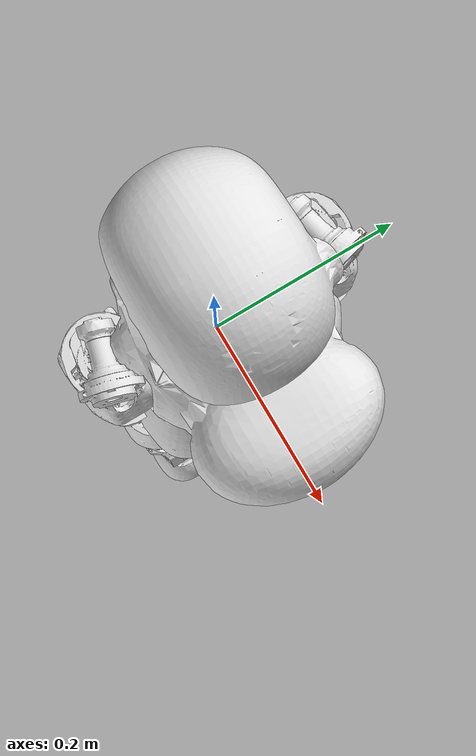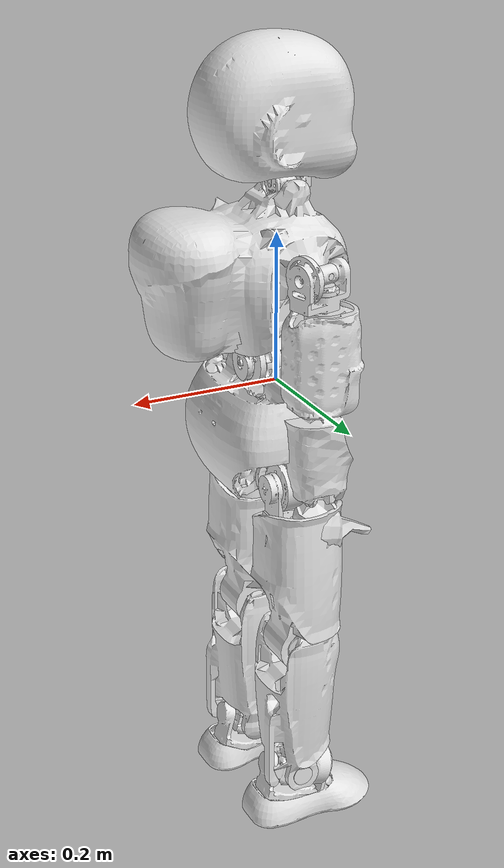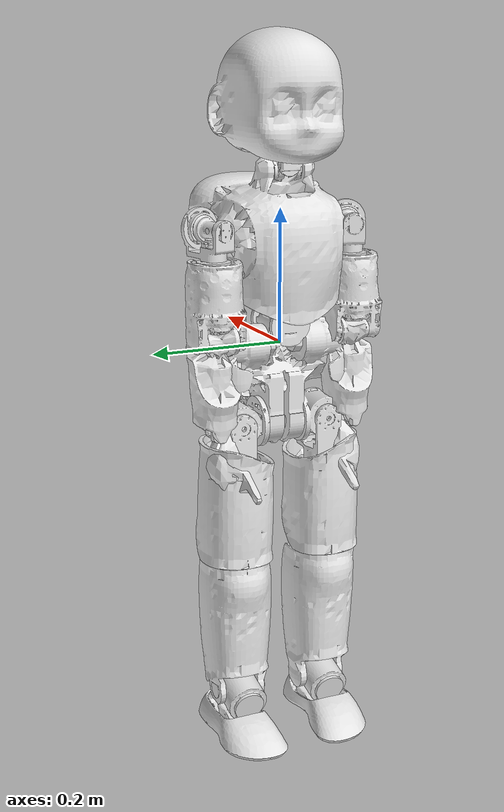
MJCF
<?xml version="1.0" ?>
<mujoco model="iCub">
	<compiler meshdir="iCub/meshes" texturedir="iCub/textures" angle="radian" autolimits="true" balanceinertia="true" boundmass="0.000001" boundinertia="0.000001"/>
	<default>
		<default class="visual">
			<geom contype="0" conaffinity="0"/>
		</default>
		<default class="collision">
			<geom rgba="0.9 0.9 0.9 0.0"/>
		</default>
	</default>
	<asset>
		<mesh name="sim_sea_2_5_root_link_prt_binary_0_0010000000474974513_0_0010000000474974513_0_0010000000474974513" file="stl/sim_sea_2-5_root_link_prt-binary.stl" scale="0.0010000000474974513 0.0010000000474974513 0.0010000000474974513"/>
		<mesh name="sim_sea_2_5_lap_belt_1_prt_binary_0_0010000000474974513_0_0010000000474974513_0_0010000000474974513" file="stl/sim_sea_2-5_lap_belt_1_prt-binary.stl" scale="0.0010000000474974513 0.0010000000474974513 0.0010000000474974513"/>
		<mesh name="sim_sea_2_5_lap_belt_2_prt_binary_0_0010000000474974513_0_0010000000474974513_0_0010000000474974513" file="stl/sim_sea_2-5_lap_belt_2_prt-binary.stl" scale="0.0010000000474974513 0.0010000000474974513 0.0010000000474974513"/>
		<mesh name="sim_sea_2_5_chest_bb_prt_binary_0_0010000000474974513_0_0010000000474974513_0_0010000000474974513" file="stl/sim_sea_2-5_chest_bb_prt-binary.stl" scale="0.0010000000474974513 0.0010000000474974513 0.0010000000474974513"/>
		<mesh name="sim_sea_2_5_neck_1_prt_binary_0_0010000000474974513_0_0010000000474974513_0_0010000000474974513" file="stl/sim_sea_2-5_neck_1_prt-binary.stl" scale="0.0010000000474974513 0.0010000000474974513 0.0010000000474974513"/>
		<mesh name="sim_sea_2_5_neck_2_prt_binary_0_0010000000474974513_0_0010000000474974513_0_0010000000474974513" file="stl/sim_sea_2-5_neck_2_prt-binary.stl" scale="0.0010000000474974513 0.0010000000474974513 0.0010000000474974513"/>
		<mesh name="sim_sea_2_5_head_prt_binary_0_0010000000474974513_0_0010000000474974513_0_0010000000474974513" file="stl/sim_sea_2-5_head_prt-binary.stl" scale="0.0010000000474974513 0.0010000000474974513 0.0010000000474974513"/>
		<mesh name="sim_sea_2_5_r_shoulder_1_prt_binary_0_0010000000474974513_0_0010000000474974513_0_0010000000474974513" file="stl/sim_sea_2-5_r_shoulder_1_prt-binary.stl" scale="0.0010000000474974513 0.0010000000474974513 0.0010000000474974513"/>
		<mesh name="sim_sea_2_5_r_shoulder_2_prt_binary_0_0010000000474974513_0_0010000000474974513_0_0010000000474974513" file="stl/sim_sea_2-5_r_shoulder_2_prt-binary.stl" scale="0.0010000000474974513 0.0010000000474974513 0.0010000000474974513"/>
		<mesh name="sim_sea_2_5_r_upper_arm_prt_binary_0_0010000000474974513_0_0010000000474974513_0_0010000000474974513" file="stl/sim_sea_2-5_r_upper_arm_prt-binary.stl" scale="0.0010000000474974513 0.0010000000474974513 0.0010000000474974513"/>
		<mesh name="sim_sea_2_5_r_elbow_prt_binary_0_0010000000474974513_0_0010000000474974513_0_0010000000474974513" file="stl/sim_sea_2-5_r_elbow_prt-binary.stl" scale="0.0010000000474974513 0.0010000000474974513 0.0010000000474974513"/>
		<mesh name="sim_sea_2_5_r_elbow_prosup_prt_binary_0_0010000000474974513_0_0010000000474974513_0_0010000000474974513" file="stl/sim_sea_2-5_r_elbow_prosup_prt-binary.stl" scale="0.0010000000474974513 0.0010000000474974513 0.0010000000474974513"/>
		<mesh name="sim_sea_2_5_r_forearm_prt_binary_0_0010000000474974513_0_0010000000474974513_0_0010000000474974513" file="stl/sim_sea_2-5_r_forearm_prt-binary.stl" scale="0.0010000000474974513 0.0010000000474974513 0.0010000000474974513"/>
		<mesh name="sim_sea_2_5_r_wrist_pitch_prt_binary_0_0010000000474974513_0_0010000000474974513_0_0010000000474974513" file="stl/sim_sea_2-5_r_wrist_pitch_prt-binary.stl" scale="0.0010000000474974513 0.0010000000474974513 0.0010000000474974513"/>
		<mesh name="sim_sea_2_5_r_hand_prt_binary_0_0010000000474974513_0_0010000000474974513_0_0010000000474974513" file="stl/sim_sea_2-5_r_hand_prt-binary.stl" scale="0.0010000000474974513 0.0010000000474974513 0.0010000000474974513"/>
		<mesh name="sim_sea_2_5_l_shoulder_1_prt_binary_0_0010000000474974513_0_0010000000474974513_0_0010000000474974513" file="stl/sim_sea_2-5_l_shoulder_1_prt-binary.stl" scale="0.0010000000474974513 0.0010000000474974513 0.0010000000474974513"/>
		<mesh name="sim_sea_2_5_l_shoulder_2_prt_binary_0_0010000000474974513_0_0010000000474974513_0_0010000000474974513" file="stl/sim_sea_2-5_l_shoulder_2_prt-binary.stl" scale="0.0010000000474974513 0.0010000000474974513 0.0010000000474974513"/>
		<mesh name="sim_sea_2_5_l_upper_arm_prt_binary_0_0010000000474974513_0_0010000000474974513_0_0010000000474974513" file="stl/sim_sea_2-5_l_upper_arm_prt-binary.stl" scale="0.0010000000474974513 0.0010000000474974513 0.0010000000474974513"/>
		<mesh name="sim_sea_2_5_l_elbow_prt_binary_0_0010000000474974513_0_0010000000474974513_0_0010000000474974513" file="stl/sim_sea_2-5_l_elbow_prt-binary.stl" scale="0.0010000000474974513 0.0010000000474974513 0.0010000000474974513"/>
		<mesh name="sim_sea_2_5_l_elbow_prosup_prt_binary_0_0010000000474974513_0_0010000000474974513_0_0010000000474974513" file="stl/sim_sea_2-5_l_elbow_prosup_prt-binary.stl" scale="0.0010000000474974513 0.0010000000474974513 0.0010000000474974513"/>
		<mesh name="sim_sea_2_5_l_forearm_prt_binary_0_0010000000474974513_0_0010000000474974513_0_0010000000474974513" file="stl/sim_sea_2-5_l_forearm_prt-binary.stl" scale="0.0010000000474974513 0.0010000000474974513 0.0010000000474974513"/>
		<mesh name="sim_sea_2_5_l_wrist_pitch_prt_binary_0_0010000000474974513_0_0010000000474974513_0_0010000000474974513" file="stl/sim_sea_2-5_l_wrist_pitch_prt-binary.stl" scale="0.0010000000474974513 0.0010000000474974513 0.0010000000474974513"/>
		<mesh name="sim_sea_2_5_l_hand_prt_binary_0_0010000000474974513_0_0010000000474974513_0_0010000000474974513" file="stl/sim_sea_2-5_l_hand_prt-binary.stl" scale="0.0010000000474974513 0.0010000000474974513 0.0010000000474974513"/>
		<mesh name="sim_sea_2_5_r_hip_1_prt_binary_0_0010000000474974513_0_0010000000474974513_0_0010000000474974513" file="stl/sim_sea_2-5_r_hip_1_prt-binary.stl" scale="0.0010000000474974513 0.0010000000474974513 0.0010000000474974513"/>
		<mesh name="sim_sea_2_5_r_hip_2_prt_binary_0_0010000000474974513_0_0010000000474974513_0_0010000000474974513" file="stl/sim_sea_2-5_r_hip_2_prt-binary.stl" scale="0.0010000000474974513 0.0010000000474974513 0.0010000000474974513"/>
		<mesh name="sim_sea_2_5_r_upper_thigh_prt_binary_0_0010000000474974513_0_0010000000474974513_0_0010000000474974513" file="stl/sim_sea_2-5_r_upper_thigh_prt-binary.stl" scale="0.0010000000474974513 0.0010000000474974513 0.0010000000474974513"/>
		<mesh name="sim_sea_2_5_r_thigh_prt_binary_0_0010000000474974513_0_0010000000474974513_0_0010000000474974513" file="stl/sim_sea_2-5_r_thigh_prt-binary.stl" scale="0.0010000000474974513 0.0010000000474974513 0.0010000000474974513"/>
		<mesh name="sim_sea_2_5_r_shank_prt_binary_0_0010000000474974513_0_0010000000474974513_0_0010000000474974513" file="stl/sim_sea_2-5_r_shank_prt-binary.stl" scale="0.0010000000474974513 0.0010000000474974513 0.0010000000474974513"/>
		<mesh name="sim_sea_2_5_r_ankle_prt_binary_0_0010000000474974513_0_0010000000474974513_0_0010000000474974513" file="stl/sim_sea_2-5_r_ankle_prt-binary.stl" scale="0.0010000000474974513 0.0010000000474974513 0.0010000000474974513"/>
		<mesh name="sim_sea_2_5_r_foot_prt_binary_0_0010000000474974513_0_0010000000474974513_0_0010000000474974513" file="stl/sim_sea_2-5_r_foot_prt-binary.stl" scale="0.0010000000474974513 0.0010000000474974513 0.0010000000474974513"/>
		<mesh name="sim_sea_2_5_r_sole_prt_binary_0_0010000000474974513_0_0010000000474974513_0_0010000000474974513" file="stl/sim_sea_2-5_r_sole_prt-binary.stl" scale="0.0010000000474974513 0.0010000000474974513 0.0010000000474974513"/>
		<mesh name="sim_sea_2_5_l_hip_1_prt_binary_0_0010000000474974513_0_0010000000474974513_0_0010000000474974513" file="stl/sim_sea_2-5_l_hip_1_prt-binary.stl" scale="0.0010000000474974513 0.0010000000474974513 0.0010000000474974513"/>
		<mesh name="sim_sea_2_5_l_hip_2_prt_binary_0_0010000000474974513_0_0010000000474974513_0_0010000000474974513" file="stl/sim_sea_2-5_l_hip_2_prt-binary.stl" scale="0.0010000000474974513 0.0010000000474974513 0.0010000000474974513"/>
		<mesh name="sim_sea_2_5_l_upper_thigh_prt_binary_0_0010000000474974513_0_0010000000474974513_0_0010000000474974513" file="stl/sim_sea_2-5_l_upper_thigh_prt-binary.stl" scale="0.0010000000474974513 0.0010000000474974513 0.0010000000474974513"/>
		<mesh name="sim_sea_2_5_l_thigh_prt_binary_0_0010000000474974513_0_0010000000474974513_0_0010000000474974513" file="stl/sim_sea_2-5_l_thigh_prt-binary.stl" scale="0.0010000000474974513 0.0010000000474974513 0.0010000000474974513"/>
		<mesh name="sim_sea_2_5_l_shank_prt_binary_0_0010000000474974513_0_0010000000474974513_0_0010000000474974513" file="stl/sim_sea_2-5_l_shank_prt-binary.stl" scale="0.0010000000474974513 0.0010000000474974513 0.0010000000474974513"/>
		<mesh name="sim_sea_2_5_l_ankle_prt_binary_0_0010000000474974513_0_0010000000474974513_0_0010000000474974513" file="stl/sim_sea_2-5_l_ankle_prt-binary.stl" scale="0.0010000000474974513 0.0010000000474974513 0.0010000000474974513"/>
		<mesh name="sim_sea_2_5_l_foot_prt_binary_0_0010000000474974513_0_0010000000474974513_0_0010000000474974513" file="stl/sim_sea_2-5_l_foot_prt-binary.stl" scale="0.0010000000474974513 0.0010000000474974513 0.0010000000474974513"/>
		<mesh name="sim_sea_2_5_l_sole_prt_binary_0_0010000000474974513_0_0010000000474974513_0_0010000000474974513" file="stl/sim_sea_2-5_l_sole_prt-binary.stl" scale="0.0010000000474974513 0.0010000000474974513 0.0010000000474974513"/>
	</asset>
	<worldbody>
		<body name="iCub" pos="0.0 0.0 0.0" quat="1.0 0.0 0.0 0.0">
			<freejoint/>
			<inertial mass="0.0" pos="0.0 0.0 0.0" quat="1.0 0.0 0.0 0.0" diaginertia="0.0 0.0 0.0"/>
			<body name="root_link" pos="0.0 0.0 0.0" quat="1.0 0.0 0.0 0.0">
				<inertial mass="5.127389907836914" pos="0.02561270073056221 0.00017707300139591098 -0.044533900916576385" quat="0.4061185419559479 0.5818752646446228 -0.40049850940704346 -0.5797325372695923" diaginertia="0.014542383141815662 0.01996362954378128 0.025951389223337173"/>
				<geom name="SM_root_link_visual_0" type="mesh" pos="-0.036400001496076584 0.0 0.03200000151991844" quat="-0.4999999701976776 -0.5 0.5 0.5" mesh="sim_sea_2_5_root_link_prt_binary_0_0010000000474974513_0_0010000000474974513_0_0010000000474974513" rgba="0.9 0.9 0.9 1.0" class="visual"/>
				<geom name="SM_root_link_collision_0" type="mesh" pos="-0.036400001496076584 0.0 0.03200000151991844" quat="-0.4999999701976776 -0.5 0.5 0.5" mesh="sim_sea_2_5_root_link_prt_binary_0_0010000000474974513_0_0010000000474974513_0_0010000000474974513" class="collision"/>
				<body name="root_link_imu_acc" pos="0.08515500277280807 -0.010999999940395355 -0.11230900138616562" quat="0.3535533547401428 -0.6123724579811096 0.6123724579811096 -0.3535533845424652">
					<inertial mass="0.0" pos="0.0 0.0 0.0" quat="1.0 0.0 0.0 0.0" diaginertia="0.0 0.0 0.0"/>
				</body>
				<body name="r_hip_1" pos="0.006451500114053488 0.026000000536441803 -0.1199129968881607" quat="4.371138828673793e-08 0.0 0.0 1.0">
					<inertial mass="0.9199780225753784" pos="-0.0005145000177435577 -0.03807530179619789 -7.100000220816582e-05" quat="0.46291396021842957 0.5310412645339966 0.4629858732223511 0.5379126071929932" diaginertia="0.000404251622967422 0.000574638310354203 0.000580144056584686"/>
					<geom name="SM_r_hip_1_visual_0" type="mesh" pos="0.04285150021314621 0.026000000536441803 0.15191300213336945" quat="0.4999999701976776 0.5 0.5 0.5" mesh="sim_sea_2_5_r_hip_1_prt_binary_0_0010000000474974513_0_0010000000474974513_0_0010000000474974513" rgba="0.9 0.9 0.9 1.0" class="visual"/>
					<geom name="SM_r_hip_1_collision_0" type="mesh" pos="0.04285150021314621 0.026000000536441803 0.15191300213336945" quat="0.4999999701976776 0.5 0.5 0.5" mesh="sim_sea_2_5_r_hip_1_prt_binary_0_0010000000474974513_0_0010000000474974513_0_0010000000474974513" class="collision"/>
					<joint name="r_hip_pitch" type="hinge" pos="0.0 0.0 0.0" range="-0.7853981852531433 2.3387413024902344" axis="0.0 -1.0 0.0"/>
					<body name="r_hip_2" pos="-8.673617379884035e-19 -0.04410000145435333 1.3877787807814457e-17" quat="1.0 0.0 0.0 0.0">
						<inertial mass="0.41836100816726685" pos="-0.0013753999955952168 3.5000000480067683e-06 -0.04428200051188469" quat="0.9846654534339905 0.0003719814703799784 0.000715636124368757 0.1744515597820282" diaginertia="0.00028160656802356243 0.0003196659090463072 0.00048786652041599154"/>
						<geom name="SM_r_hip_2_visual_0" type="mesh" pos="0.04285150021314621 0.07010000199079514 0.15191300213336945" quat="0.4999999701976776 0.5 0.5 0.5" mesh="sim_sea_2_5_r_hip_2_prt_binary_0_0010000000474974513_0_0010000000474974513_0_0010000000474974513" rgba="0.9 0.9 0.9 1.0" class="visual"/>
						<geom name="SM_r_hip_2_collision_0" type="mesh" pos="0.04285150021314621 0.07010000199079514 0.15191300213336945" quat="0.4999999701976776 0.5 0.5 0.5" mesh="sim_sea_2_5_r_hip_2_prt_binary_0_0010000000474974513_0_0010000000474974513_0_0010000000474974513" class="collision"/>
						<joint name="r_hip_roll" type="hinge" pos="-8.67360548916273e-19 -1.3877787807814457e-17 -1.3877787807814457e-17" range="-0.3490658402442932 2.094395160675049" axis="-1.0 0.0 0.0"/>
						<body name="r_hip_3" pos="-0.0008575000101700425 0.0 -0.07429999858140945" quat="-4.371138828673793e-08 1.0 -3.308722450212111e-24 -3.834885750348598e-31">
							<inertial mass="0.1262120008468628" pos="-0.0001230000052601099 -0.00028229999588802457 0.008717999793589115" quat="-0.05390265956521034 0.9220902323722839 -0.030925733968615532 -0.3819524347782135" diaginertia="0.009999729692935944 0.010000000707805157 0.01000026986002922"/>
							<geom name="SM_r_hip_3_visual_0" type="mesh" pos="0.04370899870991707 -0.07010000199079514 -0.2262129932641983" quat="0.4999999701976776 -0.5 0.5 -0.5" mesh="sim_sea_2_5_r_upper_thigh_prt_binary_0_0010000000474974513_0_0010000000474974513_0_0010000000474974513" rgba="0.9 0.9 0.9 1.0" class="visual"/>
							<geom name="SM_r_hip_3_collision_0" type="mesh" pos="0.04370899870991707 -0.07010000199079514 -0.2262129932641983" quat="0.4999999701976776 -0.5 0.5 -0.5" mesh="sim_sea_2_5_r_upper_thigh_prt_binary_0_0010000000474974513_0_0010000000474974513_0_0010000000474974513" class="collision"/>
							<body name="r_upper_leg" pos="0.0 0.0 0.014399999752640724" quat="4.371138828673793e-08 1.0 3.308722450212111e-24 -1.0517273734702544e-31">
								<inertial mass="1.8035000562667847" pos="0.0033998999278992414 -2.9099999665049836e-05 -0.07895399630069733" quat="0.9954400658607483 0.09352487325668335 -0.011569689959287643 -0.01477465033531189" diaginertia="0.0014523080317303538 0.006470563821494579 0.006481229327619076"/>
								<geom name="SM_r_upper_leg_visual_0" type="mesh" pos="0.04370899870991707 0.07010000199079514 0.2408130019903183" quat="0.4999999701976776 0.5 0.5 0.5" mesh="sim_sea_2_5_r_thigh_prt_binary_0_0010000000474974513_0_0010000000474974513_0_0010000000474974513" rgba="0.9 0.9 0.9 1.0" class="visual"/>
								<geom name="SM_r_upper_leg_collision_0" type="mesh" pos="0.04370899870991707 0.07010000199079514 0.2408130019903183" quat="0.4999999701976776 0.5 0.5 0.5" mesh="sim_sea_2_5_r_thigh_prt_binary_0_0010000000474974513_0_0010000000474974513_0_0010000000474974513" class="collision"/>
								<joint name="r_hip_yaw" type="hinge" pos="0.0 -4.852938971426682e-24 -5.551115123125783e-17" range="-1.3962633609771729 1.3962633609771729" axis="0.0 0.0 -1.0"/>
								<body name="r_upper_leg_ems_gyro_eb11" pos="-0.013081000186502934 -0.04040699824690819 -0.08797899633646011" quat="-0.4999999701976776 -0.5 -0.5 0.5">
									<inertial mass="0.0" pos="0.0 0.0 0.0" quat="1.0 0.0 0.0 0.0" diaginertia="0.0 0.0 0.0"/>
								</body>
								<body name="r_upper_leg_dh_frame" pos="0.0 0.0 -0.14582499861717224" quat="0.7071067690849304 0.7071067690849304 -9.530467973832724e-32 -3.486303480061406e-32">
									<inertial mass="0.0" pos="0.0 0.0 0.0" quat="1.0 0.0 0.0 0.0" diaginertia="0.0 0.0 0.0"/>
								</body>
								<body name="r_upper_leg_back_contact" pos="-0.05119990184903145 0.0 0.014600000344216824" quat="0.7071067690849304 2.3396117585287553e-24 0.7071067690849304 -2.3396125473896605e-24">
									<inertial mass="0.0" pos="0.0 0.0 0.0" quat="1.0 0.0 0.0 0.0" diaginertia="0.0 0.0 0.0"/>
								</body>
								<body name="r_upper_leg_ems_gyro_eb8" pos="-0.01307899970561266 0.040407199412584305 -0.03565499931573868" quat="-0.4999999701976776 -0.5 -0.5 0.5">
									<inertial mass="0.0" pos="0.0 0.0 0.0" quat="1.0 0.0 0.0 0.0" diaginertia="0.0 0.0 0.0"/>
								</body>
								<body name="r_lower_leg" pos="0.0 0.0 -0.14582499861717224" quat="1.0 0.0 0.0 -3.308722450212111e-24">
									<inertial mass="1.472000002861023" pos="0.0012362999841570854 -0.00351310009136796 -0.08879400044679642" quat="0.6274700164794922 0.7764700055122375 0.007077293004840612 -0.057668186724185944" diaginertia="0.0014801976503804326 0.004242227412760258 0.00461204256862402"/>
									<geom name="SM_r_lower_leg_visual_0" type="mesh" pos="0.04370899870991707 0.07010000199079514 0.38663798570632935" quat="0.4999999701976776 0.5 0.5 0.5" mesh="sim_sea_2_5_r_shank_prt_binary_0_0010000000474974513_0_0010000000474974513_0_0010000000474974513" rgba="0.9 0.9 0.9 1.0" class="visual"/>
									<geom name="SM_r_lower_leg_collision_0" type="mesh" pos="0.04370899870991707 0.07010000199079514 0.38663798570632935" quat="0.4999999701976776 0.5 0.5 0.5" mesh="sim_sea_2_5_r_shank_prt_binary_0_0010000000474974513_0_0010000000474974513_0_0010000000474974513" class="collision"/>
									<joint name="r_knee" type="hinge" pos="0.0 0.0 0.0" range="-2.164208173751831 0.06981316953897476" axis="0.0 -1.0 0.0"/>
									<body name="r_lower_leg_skin_0" pos="0.05441170185804367 -0.031214000657200813 -0.0026340000331401825" quat="0.24447712302207947 0.615490734577179 -0.2091393768787384 0.7194878458976746">
										<inertial mass="0.0" pos="0.0 0.0 0.0" quat="1.0 0.0 0.0 0.0" diaginertia="0.0 0.0 0.0"/>
									</body>
									<body name="r_lower_leg_skin_4" pos="0.05831030011177063 0.01678360067307949 0.007271999958902597" quat="-0.1538650542497635 0.5769519209861755 0.11175776273012161 0.7943313121795654">
										<inertial mass="0.0" pos="0.0 0.0 0.0" quat="1.0 0.0 0.0 0.0" diaginertia="0.0 0.0 0.0"/>
									</body>
									<body name="r_lower_leg_skin_6" pos="0.0520855188369751 0.030443400144577026 -0.02214900031685829" quat="-0.2723481059074402 0.6783934235572815 0.30193373560905457 0.6119189858436584">
										<inertial mass="0.0" pos="0.0 0.0 0.0" quat="1.0 0.0 0.0 0.0" diaginertia="0.0 0.0 0.0"/>
									</body>
									<body name="r_lower_leg_skin_10" pos="0.06446070224046707 0.0003423999878577888 -0.021205000579357147" quat="-0.00014429229486268014 0.7415094375610352 0.00015946189523674548 0.6709424257278442">
										<inertial mass="0.0" pos="0.0 0.0 0.0" quat="1.0 0.0 0.0 0.0" diaginertia="0.0 0.0 0.0"/>
									</body>
									<body name="r_lower_leg_skin_14" pos="0.05504769831895828 -0.031176000833511353 -0.021900000050663948" quat="0.21481208503246307 0.7040941715240479 -0.23882488906383514 0.6333007216453552">
										<inertial mass="0.0" pos="0.0 0.0 0.0" quat="1.0 0.0 0.0 0.0" diaginertia="0.0 0.0 0.0"/>
									</body>
									<body name="r_lower_leg_skin_16" pos="0.027287499979138374 -0.050287000834941864 -0.004548999946564436" quat="0.40048012137413025 0.5764744281768799 -0.3854711055755615 0.5989198088645935">
										<inertial mass="0.0" pos="0.0 0.0 0.0" quat="1.0 0.0 0.0 0.0" diaginertia="0.0 0.0 0.0"/>
									</body>
									<body name="r_lower_leg_skin_19" pos="0.03575339913368225 0.04106279835104942 0.006064999848604202" quat="-0.35557806491851807 0.5796743631362915 0.31029263138771057 0.6642743349075317">
										<inertial mass="0.0" pos="0.0 0.0 0.0" quat="1.0 0.0 0.0 0.0" diaginertia="0.0 0.0 0.0"/>
									</body>
									<body name="r_lower_leg_skin_21" pos="0.024270400404930115 0.04853779822587967 -0.02427699975669384" quat="-0.42192620038986206 0.5654088854789734 0.415502667427063 0.5741503238677979">
										<inertial mass="0.0" pos="0.0 0.0 0.0" quat="1.0 0.0 0.0 0.0" diaginertia="0.0 0.0 0.0"/>
									</body>
									<body name="r_lower_leg_skin_29" pos="0.03846637159585953 -0.043515998870134354 -0.0524200014770031" quat="0.30672216415405273 0.6457869410514832 -0.31812596321105957 0.6226367950439453">
										<inertial mass="0.0" pos="0.0 0.0 0.0" quat="1.0 0.0 0.0 0.0" diaginertia="0.0 0.0 0.0"/>
									</body>
									<body name="r_lower_leg_skin_32" pos="0.04598300904035568 0.03258470073342323 -0.08073300123214722" quat="-0.21892784535884857 0.6865805983543396 0.22979192435741425 0.6541202664375305">
										<inertial mass="0.0" pos="0.0 0.0 0.0" quat="1.0 0.0 0.0 0.0" diaginertia="0.0 0.0 0.0"/>
									</body>
									<body name="r_lower_leg_skin_36" pos="0.05322409048676491 -0.015601799823343754 -0.08836200088262558" quat="0.07115986943244934 0.722354531288147 -0.07517972588539124 0.6837310791015625">
										<inertial mass="0.0" pos="0.0 0.0 0.0" quat="1.0 0.0 0.0 0.0" diaginertia="0.0 0.0 0.0"/>
									</body>
									<body name="r_lower_leg_skin_38" pos="0.048804670572280884 -0.03126300126314163 -0.060756999999284744" quat="0.18405918776988983 0.6997822523117065 -0.19448409974575043 0.6622710227966309">
										<inertial mass="0.0" pos="0.0 0.0 0.0" quat="1.0 0.0 0.0 0.0" diaginertia="0.0 0.0 0.0"/>
									</body>
									<body name="r_lower_leg_skin_42" pos="0.05701059848070145 0.0007962000090628862 -0.05908000096678734" quat="-0.0022608069702982903 0.7533659934997559 0.002590386662632227 0.6575924754142761">
										<inertial mass="0.0" pos="0.0 0.0 0.0" quat="1.0 0.0 0.0 0.0" diaginertia="0.0 0.0 0.0"/>
									</body>
									<body name="r_lower_leg_skin_46" pos="0.055815599858760834 0.017216399312019348 -0.05017999932169914" quat="-0.10612017661333084 0.7458844184875488 0.1225181445479393 0.6460527777671814">
										<inertial mass="0.0" pos="0.0 0.0 0.0" quat="1.0 0.0 0.0 0.0" diaginertia="0.0 0.0 0.0"/>
									</body>
									<body name="r_lower_leg_skin_49" pos="0.04113136976957321 0.032438501715660095 -0.13885900378227234" quat="-0.24192273616790771 0.6867059469223022 0.2623136341571808 0.6333245038986206">
										<inertial mass="0.0" pos="0.0 0.0 0.0" quat="1.0 0.0 0.0 0.0" diaginertia="0.0 0.0 0.0"/>
									</body>
									<body name="r_lower_leg_skin_51" pos="0.051415830850601196 0.01775900088250637 -0.10820599645376205" quat="-0.09275706857442856 0.7228027582168579 0.09894247353076935 0.6776154637336731">
										<inertial mass="0.0" pos="0.0 0.0 0.0" quat="1.0 0.0 0.0 0.0" diaginertia="0.0 0.0 0.0"/>
									</body>
									<body name="r_lower_leg_skin_53" pos="0.052073121070861816 -0.0154339000582695 -0.10765399783849716" quat="0.07214782387018204 0.725584089756012 -0.07698453962802887 0.679996907711029">
										<inertial mass="0.0" pos="0.0 0.0 0.0" quat="1.0 0.0 0.0 0.0" diaginertia="0.0 0.0 0.0"/>
									</body>
									<body name="r_lower_leg_skin_55" pos="0.04350266233086586 -0.03048899956047535 -0.13814300298690796" quat="0.1994505375623703 0.7025708556175232 -0.21626229584217072 0.6479539275169373">
										<inertial mass="0.0" pos="0.0 0.0 0.0" quat="1.0 0.0 0.0 0.0" diaginertia="0.0 0.0 0.0"/>
									</body>
									<body name="r_lower_leg_skin_60" pos="0.048369668424129486 0.018055999651551247 -0.1469379961490631" quat="-0.10229667276144028 0.7267177104949951 0.11093027144670486 0.6701576113700867">
										<inertial mass="0.0" pos="0.0 0.0 0.0" quat="1.0 0.0 0.0 0.0" diaginertia="0.0 0.0 0.0"/>
									</body>
									<body name="r_ankle_1" pos="0.0 0.0 -0.2004999965429306" quat="0.9914448857307434 1.4642580728994356e-24 0.1305260956287384 -7.606257590430698e-24">
										<inertial mass="0.6802999973297119" pos="0.01514340564608574 -0.0008684999775141478 4.285908289602958e-05" quat="-0.5393762588500977 -0.2757035791873932 0.6798213124275208 -0.41340509057044983" diaginertia="0.00029954113415442407 0.00041326656355522573 0.00044868089025840163"/>
										<geom name="SM_r_ankle_1_visual_0" type="mesh" pos="-0.10974272340536118 0.07010000199079514 0.5784444808959961" quat="0.5609854459762573 0.4304593801498413 0.4304594099521637 0.5609855055809021" mesh="sim_sea_2_5_r_ankle_prt_binary_0_0010000000474974513_0_0010000000474974513_0_0010000000474974513" rgba="0.9 0.9 0.9 1.0" class="visual"/>
										<geom name="SM_r_ankle_1_collision_0" type="mesh" pos="-0.10974272340536118 0.07010000199079514 0.5784444808959961" quat="0.5609854459762573 0.4304593801498413 0.4304594099521637 0.5609855055809021" mesh="sim_sea_2_5_r_ankle_prt_binary_0_0010000000474974513_0_0010000000474974513_0_0010000000474974513" class="collision"/>
										<joint name="r_ankle_pitch" type="hinge" pos="-0.0 3.6734198463196485e-40 5.551115123125783e-17" range="-0.8726646304130554 0.3490658402442932" axis="0.0 1.0 0.0"/>
										<body name="r_ankle_2" pos="2.7755575615628914e-17 1.3877787807814457e-17 -1.1102230246251565e-16" quat="1.0 1.4092726435646877e-25 0.0 -7.687894438929305e-24">
											<inertial mass="0.2653369903564453" pos="0.0011452158214524388 -8.300000445160549e-06 -0.03851185366511345" quat="0.563768208026886 0.7319279313087463 0.23369145393371582 -0.3030432462692261" diaginertia="0.009979299269616604 0.009999999776482582 0.010020701214671135"/>
											<geom name="SM_r_ankle_2_visual_0" type="mesh" pos="-0.10974272340536118 0.07010000199079514 0.5784444808959961" quat="0.5609854459762573 0.4304593801498413 0.4304594099521637 0.5609855055809021" mesh="sim_sea_2_5_r_foot_prt_binary_0_0010000000474974513_0_0010000000474974513_0_0010000000474974513" rgba="0.9 0.9 0.9 1.0" class="visual"/>
											<geom name="SM_r_ankle_2_collision_0" type="mesh" pos="-0.10974272340536118 0.07010000199079514 0.5784444808959961" quat="0.5609854459762573 0.4304593801498413 0.4304594099521637 0.5609855055809021" mesh="sim_sea_2_5_r_foot_prt_binary_0_0010000000474974513_0_0010000000474974513_0_0010000000474974513" class="collision"/>
											<joint name="r_ankle_roll" type="hinge" pos="-1.9248370844968602e-18 1.3877789462175682e-17 1.1442298092706406e-16" range="-0.4363323152065277 0.4363323152065277" axis="-1.0 -6.013653345841754e-16 5.846629846928408e-10"/>
											<body name="r_foot" pos="-0.0034999281633645296 1.3877787807814457e-17 -0.06050034239888191" quat="-4.371138828673793e-08 1.0 -7.246768153895146e-24 1.3877787807814457e-17">
												<inertial mass="0.35788100957870483" pos="0.03977974131703377 0.004553699865937233 -0.00631181662902236" quat="0.44191473722457886 0.5497914552688599 -0.4423220753669739 0.5538879632949829" diaginertia="0.00021378160454332829 0.0010976609773933887 0.0012570865219458938"/>
												<geom name="SM_r_foot_visual_0" type="mesh" pos="-0.10624279826879501 -0.07010000199079514 -0.6387448310852051" quat="0.4304593801498413 -0.5609854459762573 0.5609855055809021 -0.4304594099521637" mesh="sim_sea_2_5_r_sole_prt_binary_0_0010000000474974513_0_0010000000474974513_0_0010000000474974513" rgba="0.9 0.9 0.9 1.0" class="visual"/>
												<geom name="SM_r_foot_collision_0" type="box" pos="0.04178579896688461 0.004997800104320049 0.000725075020454824" quat="-4.333743319762107e-08 0.9914448857307434 -5.705476979755986e-09 -0.1305260956287384" size="0.07999999821186066 0.035999998450279236 0.0005000000237487257" class="collision"/>
												<body name="r_foot_ft" pos="-2.7755575615628914e-17 0.0 1.1102230246251565e-16" quat="1.0 2.938735877055719e-39 -6.938893903907228e-18 2.481541837659083e-24">
													<inertial mass="0.0" pos="0.0 0.0 0.0" quat="1.0 0.0 0.0 0.0" diaginertia="0.0 0.0 0.0"/>
												</body>
												<body name="r_foot_dh_frame" pos="0.0 1.3877787807814457e-17 0.004000000189989805" quat="0.7071055173873901 -1.1287137538637179e-13 0.7071080803871155 -1.1287137538637179e-13">
													<inertial mass="0.0" pos="0.0 0.0 0.0" quat="1.0 0.0 0.0 0.0" diaginertia="0.0 0.0 0.0"/>
												</body>
												<body name="r_sole" pos="0.021450225263834 0.0 0.00669127656146884" quat="4.333743319762107e-08 0.9914448857307434 5.705476979755986e-09 -0.1305260956287384">
													<inertial mass="0.0" pos="0.0 0.0 0.0" quat="1.0 0.0 0.0 0.0" diaginertia="0.0 0.0 0.0"/>
												</body>
											</body>
										</body>
									</body>
									<body name="r_lower_leg_ems_gyro_eb9" pos="0.044503290206193924 0.014343500137329102 -0.08830100297927856" quat="3.408984028396844e-08 0.7798845767974854 -2.73599773947808e-08 0.6259233355522156">
										<inertial mass="0.0" pos="0.0 0.0 0.0" quat="1.0 0.0 0.0 0.0" diaginertia="0.0 0.0 0.0"/>
									</body>
									<body name="r_lower_leg_skin_5" pos="0.06365030258893967 0.0003093999985139817 -0.001972000114619732" quat="-4.654578515328467e-05 0.6390488743782043 3.8671794754918665e-05 0.769166111946106">
										<inertial mass="0.0" pos="0.0 0.0 0.0" quat="1.0 0.0 0.0 0.0" diaginertia="0.0 0.0 0.0"/>
									</body>
									<body name="r_lower_leg_skin_11" pos="0.06071079894900322 -0.01609160006046295 -0.030884999781847" quat="0.08360324800014496 0.7802181243896484 -0.10682360827922821 0.6106216907501221">
										<inertial mass="0.0" pos="0.0 0.0 0.0" quat="1.0 0.0 0.0 0.0" diaginertia="0.0 0.0 0.0"/>
									</body>
									<body name="r_lower_leg_skin_17" pos="0.02787500061094761 -0.05031200125813484 -0.023881999775767326" quat="0.39205852150917053 0.5896168947219849 -0.39486557245254517 0.5854256749153137">
										<inertial mass="0.0" pos="0.0 0.0 0.0" quat="1.0 0.0 0.0 0.0" diaginertia="0.0 0.0 0.0"/>
									</body>
									<body name="r_lower_leg_skin_28" pos="0.04087214916944504 -0.04244000092148781 -0.03275600075721741" quat="0.3092436194419861 0.6471462249755859 -0.32454320788383484 0.6166375875473022">
										<inertial mass="0.0" pos="0.0 0.0 0.0" quat="1.0 0.0 0.0 0.0" diaginertia="0.0 0.0 0.0"/>
									</body>
									<body name="r_lower_leg_skin_35" pos="0.04774865880608559 -0.031231999397277832 -0.0801130011677742" quat="0.18402938544750214 0.6992291808128357 -0.19409219920635223 0.6629780530929565">
										<inertial mass="0.0" pos="0.0 0.0 0.0" quat="1.0 0.0 0.0 0.0" diaginertia="0.0 0.0 0.0"/>
									</body>
									<body name="r_lower_leg_skin_41" pos="0.0566008985042572 -0.015912899747490883 -0.04985399916768074" quat="0.08007480949163437 0.7567764520645142 -0.09441358596086502 0.641843855381012">
										<inertial mass="0.0" pos="0.0 0.0 0.0" quat="1.0 0.0 0.0 0.0" diaginertia="0.0 0.0 0.0"/>
									</body>
									<body name="r_lower_leg_skin_47" pos="0.05264163017272949 0.017638899385929108 -0.08885999768972397" quat="-0.09006146341562271 0.7196511030197144 0.09505070745944977 0.6818772554397583">
										<inertial mass="0.0" pos="0.0 0.0 0.0" quat="1.0 0.0 0.0 0.0" diaginertia="0.0 0.0 0.0"/>
									</body>
									<body name="r_lower_leg_skin_52" pos="0.052998319268226624 0.0012663999805226922 -0.11689499765634537" quat="-0.0037120128981769085 0.7305910587310791 0.003971809055656195 0.6827936172485352">
										<inertial mass="0.0" pos="0.0 0.0 0.0" quat="1.0 0.0 0.0 0.0" diaginertia="0.0 0.0 0.0"/>
									</body>
									<body name="r_lower_leg_skin_56" pos="0.049268390983343124 -0.01512099988758564 -0.14621800184249878" quat="0.0756504014134407 0.7300828695297241 -0.08192116022109985 0.6741994619369507">
										<inertial mass="0.0" pos="0.0 0.0 0.0" quat="1.0 0.0 0.0 0.0" diaginertia="0.0 0.0 0.0"/>
									</body>
									<body name="r_lower_leg_skin_3" pos="0.05157877877354622 0.03042050078511238 -0.0028429999947547913" quat="-0.30716168880462646 0.5987781882286072 0.2665644586086273 0.689970850944519">
										<inertial mass="0.0" pos="0.0 0.0 0.0" quat="1.0 0.0 0.0 0.0" diaginertia="0.0 0.0 0.0"/>
									</body>
									<body name="r_lower_leg_skin_15" pos="0.05917080119252205 -0.0161787997931242 0.007242999970912933" quat="0.11051426082849503 0.5804485082626343 -0.07990545779466629 0.8027958869934082">
										<inertial mass="0.0" pos="0.0 0.0 0.0" quat="1.0 0.0 0.0 0.0" diaginertia="0.0 0.0 0.0"/>
									</body>
									<body name="r_lower_leg_skin_31" pos="0.03914637863636017 -0.042270999401807785 0.006326999980956316" quat="0.3413023054599762 0.5817172527313232 -0.29295864701271057 0.6777116060256958">
										<inertial mass="0.0" pos="0.0 0.0 0.0" quat="1.0 0.0 0.0 0.0" diaginertia="0.0 0.0 0.0"/>
									</body>
									<body name="r_lower_leg_skin_43" pos="0.04712542146444321 0.03236529976129532 -0.061361998319625854" quat="-0.2135869860649109 0.6837466955184937 0.2206142395734787 0.6619670987129211">
										<inertial mass="0.0" pos="0.0 0.0 0.0" quat="1.0 0.0 0.0 0.0" diaginertia="0.0 0.0 0.0"/>
									</body>
									<body name="r_lower_leg_skin_54" pos="0.045127078890800476 -0.03074900060892105 -0.1187869980931282" quat="0.19305725395679474 0.702477216720581 -0.2077626734972 0.6527552008628845">
										<inertial mass="0.0" pos="0.0 0.0 0.0" quat="1.0 0.0 0.0 0.0" diaginertia="0.0 0.0 0.0"/>
									</body>
									<body name="r_lower_leg_skin_9" pos="0.05982140079140663 0.016797300428152084 -0.03096199966967106" quat="-0.11722982674837112 0.7690824866294861 0.14762870967388153 0.6107168197631836">
										<inertial mass="0.0" pos="0.0 0.0 0.0" quat="1.0 0.0 0.0 0.0" diaginertia="0.0 0.0 0.0"/>
									</body>
									<body name="r_lower_leg_skin_37" pos="0.055257201194763184 0.000964400009252131 -0.07831799983978271" quat="-0.0026001648511737585 0.7237334251403809 0.0027266349643468857 0.6900693774223328">
										<inertial mass="0.0" pos="0.0 0.0 0.0" quat="1.0 0.0 0.0 0.0" diaginertia="0.0 0.0 0.0"/>
									</body>
									<body name="r_lower_leg_skin_61" pos="0.0516195185482502 0.0014266000362113118 -0.13616900146007538" quat="-0.00449023162946105 0.7330275774002075 0.00483911344781518 0.6801668405532837">
										<inertial mass="0.0" pos="0.0 0.0 0.0" quat="1.0 0.0 0.0 0.0" diaginertia="0.0 0.0 0.0"/>
									</body>
									<body name="r_lower_leg_skin_20" pos="0.023441899567842484 0.04799079895019531 -0.004951999988406897" quat="-0.43517857789993286 0.5479961633682251 0.4054737389087677 0.5881418585777283">
										<inertial mass="0.0" pos="0.0 0.0 0.0" quat="1.0 0.0 0.0 0.0" diaginertia="0.0 0.0 0.0"/>
									</body>
									<body name="r_lower_leg_skin_50" pos="0.0430169478058815 0.03252730146050453 -0.11946900188922882" quat="-0.23225760459899902 0.6881741285324097 0.24955973029136658 0.6404629349708557">
										<inertial mass="0.0" pos="0.0 0.0 0.0" quat="1.0 0.0 0.0 0.0" diaginertia="0.0 0.0 0.0"/>
									</body>
								</body>
							</body>
							<body name="r_leg_ft" pos="0.0 0.0 -2.7755575615628914e-17" quat="1.0 3.308722450212111e-24 3.944304526105059e-31 3.308722450212111e-24">
								<inertial mass="0.0" pos="0.0 0.0 0.0" quat="1.0 0.0 0.0 0.0" diaginertia="0.0 0.0 0.0"/>
							</body>
						</body>
					</body>
				</body>
				<body name="l_hip_1" pos="0.006451500114053488 -0.026000000536441803 -0.1199129968881607" quat="4.371138828673793e-08 0.0 0.0 1.0">
					<inertial mass="0.9197250008583069" pos="-0.0005107999895699322 0.03809230029582977 -8.299999899463728e-05" quat="0.5398035645484924 0.452900767326355 0.5460818409919739 0.453086793422699" diaginertia="0.00040452543180435896 0.0005731289857067168 0.0005791815929114819"/>
					<geom name="SM_l_hip_1_visual_0" type="mesh" pos="0.04285150021314621 -0.026000000536441803 0.15191300213336945" quat="0.4999999701976776 0.5 0.5 0.5" mesh="sim_sea_2_5_l_hip_1_prt_binary_0_0010000000474974513_0_0010000000474974513_0_0010000000474974513" rgba="0.9 0.9 0.9 1.0" class="visual"/>
					<geom name="SM_l_hip_1_collision_0" type="mesh" pos="0.04285150021314621 -0.026000000536441803 0.15191300213336945" quat="0.4999999701976776 0.5 0.5 0.5" mesh="sim_sea_2_5_l_hip_1_prt_binary_0_0010000000474974513_0_0010000000474974513_0_0010000000474974513" class="collision"/>
					<joint name="l_hip_pitch" type="hinge" pos="0.0 0.0 0.0" range="-0.7853981852531433 2.3387413024902344" axis="0.0 -1.0 0.0"/>
					<body name="l_hip_2" pos="-8.673617379884035e-19 0.04410000145435333 1.3877787807814457e-17" quat="1.0 0.0 0.0 0.0">
						<inertial mass="0.4211060106754303" pos="-0.0015762000111863017 -1.9400000383029692e-05 -0.04405299946665764" quat="0.9805272221565247 -0.0004254594387020916 -0.00043122973875142634 0.1963823139667511" diaginertia="0.00028235267382115126 0.0003253910399507731 0.0004942842642776668"/>
						<geom name="SM_l_hip_2_visual_0" type="mesh" pos="0.04285150021314621 -0.07010000199079514 0.15191300213336945" quat="0.4999999701976776 0.5 0.5 0.5" mesh="sim_sea_2_5_l_hip_2_prt_binary_0_0010000000474974513_0_0010000000474974513_0_0010000000474974513" rgba="0.9 0.9 0.9 1.0" class="visual"/>
						<geom name="SM_l_hip_2_collision_0" type="mesh" pos="0.04285150021314621 -0.07010000199079514 0.15191300213336945" quat="0.4999999701976776 0.5 0.5 0.5" mesh="sim_sea_2_5_l_hip_2_prt_binary_0_0010000000474974513_0_0010000000474974513_0_0010000000474974513" class="collision"/>
						<joint name="l_hip_roll" type="hinge" pos="-8.673629787593224e-19 1.3877787807814457e-17 -1.3877787807814457e-17" range="-0.3490658402442932 2.094395160675049" axis="1.0 0.0 0.0"/>
						<body name="l_hip_3" pos="-0.0008575000101700425 0.0 -0.07429999858140945" quat="-4.371138828673793e-08 1.0 -3.308722450212111e-24 -3.834885750348598e-31">
							<inertial mass="0.1262120008468628" pos="-0.0001230000052601099 -0.00028229999588802457 0.008717999793589115" quat="-0.05390265956521034 0.9220902323722839 -0.030925733968615532 -0.3819524347782135" diaginertia="0.009999729692935944 0.010000000707805157 0.01000026986002922"/>
							<geom name="SM_l_hip_3_visual_0" type="mesh" pos="0.04370899870991707 0.07010000199079514 -0.2262129932641983" quat="0.4999999701976776 -0.5 0.5 -0.5" mesh="sim_sea_2_5_l_upper_thigh_prt_binary_0_0010000000474974513_0_0010000000474974513_0_0010000000474974513" rgba="0.9 0.9 0.9 1.0" class="visual"/>
							<geom name="SM_l_hip_3_collision_0" type="mesh" pos="0.04370899870991707 0.07010000199079514 -0.2262129932641983" quat="0.4999999701976776 -0.5 0.5 -0.5" mesh="sim_sea_2_5_l_upper_thigh_prt_binary_0_0010000000474974513_0_0010000000474974513_0_0010000000474974513" class="collision"/>
							<body name="l_upper_leg" pos="0.0 0.0 0.014399999752640724" quat="4.371138828673793e-08 1.0 3.308722450212111e-24 -1.0517273734702544e-31">
								<inertial mass="1.80840003490448" pos="0.0033867999445647 0.00010179999662796035 -0.07891599833965302" quat="0.9992052316665649 -0.03536369279026985 0.011863180436193943 -0.014057224616408348" diaginertia="0.0014557037502527237 0.006479881703853607 0.006488238926976919"/>
								<geom name="SM_l_upper_leg_visual_0" type="mesh" pos="0.04370899870991707 -0.07010000199079514 0.2408130019903183" quat="0.4999999701976776 0.5 0.5 0.5" mesh="sim_sea_2_5_l_thigh_prt_binary_0_0010000000474974513_0_0010000000474974513_0_0010000000474974513" rgba="0.9 0.9 0.9 1.0" class="visual"/>
								<geom name="SM_l_upper_leg_collision_0" type="mesh" pos="0.04370899870991707 -0.07010000199079514 0.2408130019903183" quat="0.4999999701976776 0.5 0.5 0.5" mesh="sim_sea_2_5_l_thigh_prt_binary_0_0010000000474974513_0_0010000000474974513_0_0010000000474974513" class="collision"/>
								<joint name="l_hip_yaw" type="hinge" pos="0.0 -2.426469485713341e-24 -2.7755575615628914e-17" range="-1.3962633609771729 1.3962633609771729" axis="0.0 0.0 1.0"/>
								<body name="l_upper_leg_ems_gyro_eb10" pos="-0.01307899970561266 0.04040699824690819 -0.03565499931573868" quat="-0.4999999701976776 0.5 0.5 0.5">
									<inertial mass="0.0" pos="0.0 0.0 0.0" quat="1.0 0.0 0.0 0.0" diaginertia="0.0 0.0 0.0"/>
								</body>
								<body name="l_upper_leg_dh_frame" pos="0.0 0.0 -0.14582499861717224" quat="0.7071067690849304 0.7071067690849304 -9.530467973832724e-32 -3.486303480061406e-32">
									<inertial mass="0.0" pos="0.0 0.0 0.0" quat="1.0 0.0 0.0 0.0" diaginertia="0.0 0.0 0.0"/>
								</body>
								<body name="l_upper_leg_back_contact" pos="-0.0512567013502121 0.0 0.014600000344216824" quat="0.7071067690849304 2.3396117585287553e-24 0.7071067690849304 -2.3396125473896605e-24">
									<inertial mass="0.0" pos="0.0 0.0 0.0" quat="1.0 0.0 0.0 0.0" diaginertia="0.0 0.0 0.0"/>
								</body>
								<body name="l_upper_leg_ems_gyro_eb6" pos="-0.013081000186502934 -0.040407199412584305 -0.08797899633646011" quat="-0.4999999701976776 -0.5 -0.5 0.5">
									<inertial mass="0.0" pos="0.0 0.0 0.0" quat="1.0 0.0 0.0 0.0" diaginertia="0.0 0.0 0.0"/>
								</body>
								<body name="l_lower_leg" pos="0.0 0.0 -0.14582499861717224" quat="1.0 0.0 0.0 -3.308722450212111e-24">
									<inertial mass="1.4723999500274658" pos="0.0009997000452131033 0.0034968999680131674 -0.08856700360774994" quat="-0.6159096360206604 0.7858185768127441 -0.0026940908282995224 -0.05601136013865471" diaginertia="0.0014846056001260877 0.004236162174493074 0.0046085030771791935"/>
									<geom name="SM_l_lower_leg_visual_0" type="mesh" pos="0.04370899870991707 -0.07010000199079514 0.38663798570632935" quat="0.4999999701976776 0.5 0.5 0.5" mesh="sim_sea_2_5_l_shank_prt_binary_0_0010000000474974513_0_0010000000474974513_0_0010000000474974513" rgba="0.9 0.9 0.9 1.0" class="visual"/>
									<geom name="SM_l_lower_leg_collision_0" type="mesh" pos="0.04370899870991707 -0.07010000199079514 0.38663798570632935" quat="0.4999999701976776 0.5 0.5 0.5" mesh="sim_sea_2_5_l_shank_prt_binary_0_0010000000474974513_0_0010000000474974513_0_0010000000474974513" class="collision"/>
									<joint name="l_knee" type="hinge" pos="0.0 0.0 0.0" range="-2.164208173751831 0.06981316953897476" axis="0.0 -1.0 0.0"/>
									<body name="l_ankle_1" pos="0.0 0.0 -0.2004999965429306" quat="0.9914448857307434 1.4642580728994356e-24 0.1305260956287384 -7.606257590430698e-24">
										<inertial mass="0.6797999739646912" pos="0.01515297219157219 0.0009021000005304813 4.2316554754506797e-05" quat="0.5531172752380371 0.5721993446350098 0.44770604372024536 -0.4076867401599884" diaginertia="0.00029876577900722623 0.0004132568428758532 0.00044794302084483206"/>
										<geom name="SM_l_ankle_1_visual_0" type="mesh" pos="-0.10974272340536118 -0.07010000199079514 0.5784444808959961" quat="0.5609854459762573 0.4304593801498413 0.4304594099521637 0.5609855055809021" mesh="sim_sea_2_5_l_ankle_prt_binary_0_0010000000474974513_0_0010000000474974513_0_0010000000474974513" rgba="0.9 0.9 0.9 1.0" class="visual"/>
										<geom name="SM_l_ankle_1_collision_0" type="mesh" pos="-0.10974272340536118 -0.07010000199079514 0.5784444808959961" quat="0.5609854459762573 0.4304593801498413 0.4304594099521637 0.5609855055809021" mesh="sim_sea_2_5_l_ankle_prt_binary_0_0010000000474974513_0_0010000000474974513_0_0010000000474974513" class="collision"/>
										<joint name="l_ankle_pitch" type="hinge" pos="-0.0 3.6734198463196485e-40 5.551115123125783e-17" range="-0.8726646304130554 0.3490658402442932" axis="0.0 1.0 0.0"/>
										<body name="l_ankle_2" pos="2.7755575615628914e-17 -1.3877787807814457e-17 -1.1102230246251565e-16" quat="1.0 1.4092726435646877e-25 0.0 -7.687894438929305e-24">
											<inertial mass="0.2653369903564453" pos="0.0011452158214524388 -8.300000445160549e-06 -0.03851185366511345" quat="0.563768208026886 0.7319279313087463 0.23369145393371582 -0.3030432462692261" diaginertia="0.009979299269616604 0.009999999776482582 0.010020701214671135"/>
											<geom name="SM_l_ankle_2_visual_0" type="mesh" pos="-0.10974272340536118 -0.07010000199079514 0.5784444808959961" quat="0.5609854459762573 0.4304593801498413 0.4304594099521637 0.5609855055809021" mesh="sim_sea_2_5_l_foot_prt_binary_0_0010000000474974513_0_0010000000474974513_0_0010000000474974513" rgba="0.9 0.9 0.9 1.0" class="visual"/>
											<geom name="SM_l_ankle_2_collision_0" type="mesh" pos="-0.10974272340536118 -0.07010000199079514 0.5784444808959961" quat="0.5609854459762573 0.4304593801498413 0.4304594099521637 0.5609855055809021" mesh="sim_sea_2_5_l_foot_prt_binary_0_0010000000474974513_0_0010000000474974513_0_0010000000474974513" class="collision"/>
											<joint name="l_ankle_roll" type="hinge" pos="-1.9248348097501757e-18 -1.3877785326272619e-17 1.1442298092706406e-16" range="-0.4363323152065277 0.4363323152065277" axis="1.0 -6.013653345841754e-16 -5.846630957151433e-10"/>
											<body name="l_foot" pos="-0.0034999281633645296 0.0 -0.06050034239888191" quat="4.371138828673793e-08 1.0 -2.724810960826365e-24 1.8495703015555604e-31">
												<inertial mass="0.35788100957870483" pos="0.03975093364715576 -0.004553699865937233 -0.006325837690383196" quat="0.4167051911354065 0.5691444873809814 -0.42052388191223145 0.5706058144569397" diaginertia="0.00021397951059043407 0.0010967772686854005 0.001256016199477017"/>
												<geom name="SM_l_foot_visual_0" type="mesh" pos="-0.10624280571937561 0.07010000199079514 -0.6387448310852051" quat="0.4304593801498413 -0.5609854459762573 0.5609855055809021 -0.4304594099521637" mesh="sim_sea_2_5_l_sole_prt_binary_0_0010000000474974513_0_0010000000474974513_0_0010000000474974513" rgba="0.9 0.9 0.9 1.0" class="visual"/>
												<geom name="SM_l_foot_collision_0" type="box" pos="0.04178579896688461 -0.004997800104320049 0.000725075020454824" quat="-4.333743319762107e-08 0.9914448857307434 -5.705476979755986e-09 -0.1305260956287384" size="0.07999999821186066 0.035999998450279236 0.0005000000237487257" class="collision"/>
												<body name="l_foot_ft" pos="-2.7755575615628914e-17 1.3877787807814457e-17 1.1102230246251565e-16" quat="1.0 9.244463733058732e-33 -4.163336342344337e-17 -5.790264287871194e-24">
													<inertial mass="0.0" pos="0.0 0.0 0.0" quat="1.0 0.0 0.0 0.0" diaginertia="0.0 0.0 0.0"/>
												</body>
												<body name="l_sole" pos="0.021450225263834 1.3877787807814457e-17 0.00669127656146884" quat="4.333743319762107e-08 0.9914448857307434 5.705476979755986e-09 -0.1305260956287384">
													<inertial mass="0.0" pos="0.0 0.0 0.0" quat="1.0 0.0 0.0 0.0" diaginertia="0.0 0.0 0.0"/>
												</body>
												<body name="l_foot_dh_frame" pos="0.0 1.3877787807814457e-17 0.004000000189989805" quat="0.7071055173873901 -1.1287137538637179e-13 0.7071080803871155 -1.1287137538637179e-13">
													<inertial mass="0.0" pos="0.0 0.0 0.0" quat="1.0 0.0 0.0 0.0" diaginertia="0.0 0.0 0.0"/>
												</body>
											</body>
										</body>
									</body>
									<body name="l_lower_leg_ems_gyro_eb7" pos="0.044503290206193924 0.011818500235676765 -0.08830100297927856" quat="3.408984028396844e-08 0.7798845767974854 -2.73599773947808e-08 0.6259233355522156">
										<inertial mass="0.0" pos="0.0 0.0 0.0" quat="1.0 0.0 0.0 0.0" diaginertia="0.0 0.0 0.0"/>
									</body>
								</body>
							</body>
							<body name="l_leg_ft" pos="0.0 0.0 -2.7755575615628914e-17" quat="1.0 3.308722450212111e-24 3.944304526105059e-31 3.308722450212111e-24">
								<inertial mass="0.0" pos="0.0 0.0 0.0" quat="1.0 0.0 0.0 0.0" diaginertia="0.0 0.0 0.0"/>
							</body>
						</body>
					</body>
				</body>
				<body name="base_link" pos="0.0 0.0 0.0" quat="1.0 0.0 0.0 0.0">
					<inertial mass="0.0" pos="0.0 0.0 0.0" quat="1.0 0.0 0.0 0.0" diaginertia="0.0 0.0 0.0"/>
				</body>
				<body name="root_link_ems_gyro_eb5" pos="0.04933080077171326 -0.012577099725604057 -0.11569099873304367" quat="0.6018152236938477 -8.603283419006402e-09 0.7986353635787964 -8.603283419006402e-09">
					<inertial mass="0.0" pos="0.0 0.0 0.0" quat="1.0 0.0 0.0 0.0" diaginertia="0.0 0.0 0.0"/>
				</body>
				<body name="torso_1" pos="0.0 0.026934800669550896 0.0" quat="-0.4999999701976776 -0.5 0.5 0.5">
					<inertial mass="0.6714400053024292" pos="0.02698063664138317 0.029147980734705925 -0.0004398000019136816" quat="-0.7027708888053894 -0.04283515363931656 0.7100430130958557 -0.010824806988239288" diaginertia="0.00029893990722484887 0.000384586863219738 0.00040916920988820493"/>
					<geom name="SM_torso_1_visual_0" type="mesh" pos="0.026934800669550896 0.03200000151991844 0.036400001496076584" quat="1.0 0.0 0.0 0.0" mesh="sim_sea_2_5_lap_belt_1_prt_binary_0_0010000000474974513_0_0010000000474974513_0_0010000000474974513" rgba="0.9 0.9 0.9 1.0" class="visual"/>
					<geom name="SM_torso_1_collision_0" type="mesh" pos="0.026934800669550896 0.03200000151991844 0.036400001496076584" quat="1.0 0.0 0.0 0.0" mesh="sim_sea_2_5_lap_belt_1_prt_binary_0_0010000000474974513_0_0010000000474974513_0_0010000000474974513" class="collision"/>
					<joint name="torso_pitch" type="hinge" pos="0.0 0.0 0.0" range="-0.3490658402442932 1.2217304706573486" axis="1.0 0.0 0.0"/>
					<body name="torso_2" pos="0.026934800669550896 0.03200000151991844 -0.057344600558280945" quat="1.0 -3.308722450212111e-24 2.956794639883555e-24 1.0322984501915584e-31">
						<inertial mass="0.42568498849868774" pos="-0.00011350781278451905 0.03615250065922737 0.05709629878401756" quat="0.49982813000679016 0.5001415014266968 -0.49965229630470276 0.5003777742385864" diaginertia="0.00043651682790368795 0.0006048021605238318 0.0008292340207844973"/>
						<geom name="SM_torso_2_visual_0" type="mesh" pos="0.0 0.14329999685287476 0.03865310177206993" quat="1.0 0.0 0.0 0.0" mesh="sim_sea_2_5_lap_belt_2_prt_binary_0_0010000000474974513_0_0010000000474974513_0_0010000000474974513" rgba="0.9 0.9 0.9 1.0" class="visual"/>
						<geom name="SM_torso_2_collision_0" type="mesh" pos="0.0 0.14329999685287476 0.03865310177206993" quat="1.0 0.0 0.0 0.0" mesh="sim_sea_2_5_lap_belt_2_prt_binary_0_0010000000474974513_0_0010000000474974513_0_0010000000474974513" class="collision"/>
						<joint name="torso_roll" type="hinge" pos="-6.938893903907228e-18 -1.5165433053113218e-25 -3.469446745158461e-18" range="-0.5235987901687622 0.5235987901687622" axis="0.0 0.0 -1.0"/>
						<body name="chest" pos="-1.9669563813964847e-25 0.05000000074505806 0.06284210085868835" quat="1.0 -3.308722450212111e-24 2.956794639883555e-24 1.0322984501915584e-31">
							<inertial mass="7.638000011444092" pos="0.0001886191894300282 0.07309100031852722 -0.047238100320100784" quat="0.5025709867477417 0.5027893781661987 0.5088938474655151 0.48544031381607056" diaginertia="0.026044152677059174 0.04303387179970741 0.04409436136484146"/>
							<geom name="SM_chest_visual_0" type="mesh" pos="0.0 0.09279999881982803 -0.024188999086618423" quat="1.0 0.0 0.0 0.0" mesh="sim_sea_2_5_chest_bb_prt_binary_0_0010000000474974513_0_0010000000474974513_0_0010000000474974513" rgba="0.9 0.9 0.9 1.0" class="visual"/>
							<geom name="SM_chest_collision_0" type="mesh" pos="0.0 0.09279999881982803 -0.024188999086618423" quat="1.0 0.0 0.0 0.0" mesh="sim_sea_2_5_chest_bb_prt_binary_0_0010000000474974513_0_0010000000474974513_0_0010000000474974513" class="collision"/>
							<joint name="torso_yaw" type="hinge" pos="-6.938893903907228e-18 -1.3877787807814457e-17 7.132304436547577e-25" range="-0.8726646304130554 0.8726646304130554" axis="0.0 -1.0 0.0"/>
							<body name="chest_ems_gyro_eb2" pos="0.016037100926041603 0.08755899965763092 -0.06534790247678757" quat="0.13052615523338318 3.9589590414834674e-06 0.9914448857307434 4.814754674953292e-07">
								<inertial mass="0.0" pos="0.0 0.0 0.0" quat="1.0 0.0 0.0 0.0" diaginertia="0.0 0.0 0.0"/>
							</body>
							<body name="chest_ems_gyro_eb4" pos="-0.06657840311527252 0.08755899965763092 -0.05180539935827255" quat="-0.13052615523338318 3.9589590414834674e-06 0.9914448857307434 -4.814754674953292e-07">
								<inertial mass="0.0" pos="0.0 0.0 0.0" quat="1.0 0.0 0.0 0.0" diaginertia="0.0 0.0 0.0"/>
							</body>
							<body name="r_shoulder_1" pos="-0.12001600116491318 0.09279999881982803 0.007969300262629986" quat="-4.222195926217864e-08 0.2588191032409668 1.1313343151186928e-08 0.9659258127212524">
								<inertial mass="0.11486200243234634" pos="-0.012265601195394993 3.199999991920777e-05 -0.0032106428407132626" quat="0.001155529054813087 0.92384272813797 0.008853713981807232 0.3826681673526764" diaginertia="0.009996443055570126 0.010000000707805157 0.010003556497395039"/>
								<geom name="SM_r_shoulder_1_visual_0" type="mesh" pos="0.09900792688131332 0.0 -0.02652924880385399" quat="1.0 0.0 0.0 0.0" mesh="sim_sea_2_5_r_shoulder_1_prt_binary_0_0010000000474974513_0_0010000000474974513_0_0010000000474974513" rgba="0.9 0.9 0.9 1.0" class="visual"/>
								<geom name="SM_r_shoulder_1_collision_0" type="mesh" pos="0.09900792688131332 0.0 -0.02652924880385399" quat="1.0 0.0 0.0 0.0" mesh="sim_sea_2_5_r_shoulder_1_prt_binary_0_0010000000474974513_0_0010000000474974513_0_0010000000474974513" class="collision"/>
								<joint name="r_shoulder_pitch" type="hinge" pos="0.0 0.0 -0.0" range="-1.6667894124984741 0.1745329201221466" axis="-0.9659258127212524 0.0 0.2588191330432892"/>
								<body name="r_shoulder_2" pos="-0.007580465637147427 0.0 0.014210246503353119" quat="0.7071068286895752 -0.18301273882389069 9.574594628247723e-08 -0.6830126643180847">
									<inertial mass="0.23816199600696564" pos="-0.021414170041680336 0.00027172526461072266 -0.01944023370742798" quat="0.922309160232544 0.01733805425465107 -0.382027268409729 -0.05568141117691994" diaginertia="0.009989659301936626 0.010000025853514671 0.010010315105319023"/>
									<geom name="SM_r_shoulder_2_visual_0" type="mesh" pos="0.10658780485391617 2.3191471143491071e-07 -0.040739212185144424" quat="1.0 0.0 0.0 0.0" mesh="sim_sea_2_5_r_shoulder_2_prt_binary_0_0010000000474974513_0_0010000000474974513_0_0010000000474974513" rgba="0.9 0.9 0.9 1.0" class="visual"/>
									<geom name="SM_r_shoulder_2_collision_0" type="mesh" pos="0.10658780485391617 2.3191471143491071e-07 -0.040739212185144424" quat="1.0 0.0 0.0 0.0" mesh="sim_sea_2_5_r_shoulder_2_prt_binary_0_0010000000474974513_0_0010000000474974513_0_0010000000474974513" class="collision"/>
									<joint name="r_shoulder_roll" type="hinge" pos="6.938894731087841e-18 -6.066173221245287e-25 1.2018516574186153e-17" range="0.0 2.8064894676208496" axis="-0.25881898403167725 2.0285224785601265e-17 -0.9659258127212524"/>
									<body name="r_shoulder_3" pos="-0.025346070528030396 2.3275042337900231e-07 -0.00538764800876379" quat="0.9914448857307434 -0.12607857584953308 -9.772560538579e-09 0.03378264233469963">
										<inertial mass="0.35912999510765076" pos="-0.02676207758486271 -7.000000096013537e-06 0.014699921011924744" quat="-0.3826795220375061 -0.0010895980522036552 0.9238700866699219 0.004395272117108107" diaginertia="0.009950555860996246 0.009999996051192284 0.010049448348581791"/>
										<geom name="SM_r_shoulder_3_visual_0" type="mesh" pos="0.13193388283252716 0.0 -0.03535156697034836" quat="1.0 0.0 0.0 0.0" mesh="sim_sea_2_5_r_upper_arm_prt_binary_0_0010000000474974513_0_0010000000474974513_0_0010000000474974513" rgba="0.9 0.9 0.9 1.0" class="visual"/>
										<geom name="SM_r_shoulder_3_collision_0" type="mesh" pos="0.13193388283252716 0.0 -0.03535156697034836" quat="1.0 0.0 0.0 0.0" mesh="sim_sea_2_5_r_upper_arm_prt_binary_0_0010000000474974513_0_0010000000474974513_0_0010000000474974513" class="collision"/>
										<joint name="r_shoulder_yaw" type="hinge" pos="1.457098335910737e-17 -6.221246066526635e-18 2.7569833863441356e-17" range="-0.6457718014717102 1.3962633609771729" axis="0.9659258723258972 2.220446049250313e-16 -0.25881895422935486"/>
										<body name="r_upper_arm" pos="-0.050897300243377686 -1.3877787807814457e-17 0.02916703000664711" quat="0.7933533191680908 1.028177006949186e-23 -0.6087614893913269 -2.146307359464942e-25">
											<inertial mass="0.7451040148735046" pos="-0.006087000016123056 0.00012599999899975955 0.029312100261449814" quat="0.52651047706604 0.5379983186721802 -0.46434250473976135 -0.46661603450775146" diaginertia="0.0005080046830698848 0.0006007513729855418 0.0006685119587928057"/>
											<geom name="SM_r_upper_arm_visual_0" type="mesh" pos="-0.014999999664723873 0.0 -0.19329999387264252" quat="0.7933533191680908 0.0 0.6087614893913269 0.0" mesh="sim_sea_2_5_r_elbow_prt_binary_0_0010000000474974513_0_0010000000474974513_0_0010000000474974513" rgba="0.9 0.9 0.9 1.0" class="visual"/>
											<geom name="SM_r_upper_arm_collision_0" type="mesh" pos="-0.014999999664723873 0.0 -0.19329999387264252" quat="0.7933533191680908 0.0 0.6087614893913269 0.0" mesh="sim_sea_2_5_r_elbow_prt_binary_0_0010000000474974513_0_0010000000474974513_0_0010000000474974513" class="collision"/>
											<body name="r_elbow_1" pos="0.0 -0.022499900311231613 0.07925999909639359" quat="0.7933533191680908 9.523875110244394e-24 0.6087614893913269 7.596979008463488e-24">
												<inertial mass="0.26790300011634827" pos="-0.006739129312336445 0.018801899626851082 -0.004657692275941372" quat="0.38010796904563904 0.17139850556850433 0.8780151605606079 -0.2350102663040161" diaginertia="0.009985174983739853 0.010003650560975075 0.010011174716055393"/>
												<geom name="SM_r_elbow_1_visual_0" type="mesh" pos="0.2593904733657837 0.022499900311231613 -0.08503258973360062" quat="1.0 0.0 0.0 0.0" mesh="sim_sea_2_5_r_elbow_prosup_prt_binary_0_0010000000474974513_0_0010000000474974513_0_0010000000474974513" rgba="0.9 0.9 0.9 1.0" class="visual"/>
												<geom name="SM_r_elbow_1_collision_0" type="mesh" pos="0.2593904733657837 0.022499900311231613 -0.08503258973360062" quat="1.0 0.0 0.0 0.0" mesh="sim_sea_2_5_r_elbow_prosup_prt_binary_0_0010000000474974513_0_0010000000474974513_0_0010000000474974513" class="collision"/>
												<joint name="r_elbow" type="hinge" pos="1.1808853320705936e-24 -1.3877786153453232e-17 1.3877789462175682e-17" range="0.2617993950843811 1.8500490188598633" axis="0.0 1.0 0.0"/>
												<body name="r_forearm" pos="-0.038462430238723755 0.022499900311231613 -0.005223168060183525" quat="1.0 0.0 -1.3877787807814457e-17 0.0">
													<inertial mass="0.6347000002861023" pos="-0.04043911397457123 -0.0003279999946244061 0.005327334627509117" quat="-0.6888680458068848 0.6932096481323242 -0.15143513679504395 0.1482856273651123" diaginertia="0.00032207401818595827 0.0006015939870849252 0.0006722920225001872"/>
													<geom name="SM_r_forearm_visual_0" type="mesh" pos="0.29688698053359985 0.0 -0.079550601541996" quat="1.0 0.0 0.0 0.0" mesh="sim_sea_2_5_r_forearm_prt_binary_0_0010000000474974513_0_0010000000474974513_0_0010000000474974513" rgba="0.9 0.9 0.9 1.0" class="visual"/>
													<geom name="SM_r_forearm_collision_0" type="mesh" pos="0.29688698053359985 0.0 -0.079550601541996" quat="1.0 0.0 0.0 0.0" mesh="sim_sea_2_5_r_forearm_prt_binary_0_0010000000474974513_0_0010000000474974513_0_0010000000474974513" class="collision"/>
													<joint name="r_wrist_prosup" type="hinge" pos="3.4715355830003106e-18 2.7755575615628914e-17 6.2534767455044574e-18" range="-1.0471975803375244 1.0471975803375244" axis="0.9659258723258972 2.220446049250313e-16 -0.25881895422935486"/>
													<body name="r_forearm_skin_1" pos="-0.033372893929481506 0.028826000168919563 -0.019845686852931976" quat="-0.1223270446062088 0.06461271643638611 0.7976725697517395 0.5870091319084167">
														<inertial mass="0.0" pos="0.0 0.0 0.0" quat="1.0 0.0 0.0 0.0" diaginertia="0.0 0.0 0.0"/>
													</body>
													<body name="r_forearm_skin_3" pos="-0.04556729272007942 -0.030890999361872673 -0.006330009084194899" quat="-0.12107653170824051 -0.0659434050321579 0.7451797127723694 -0.6524562239646912">
														<inertial mass="0.0" pos="0.0 0.0 0.0" quat="1.0 0.0 0.0 0.0" diaginertia="0.0 0.0 0.0"/>
													</body>
													<body name="r_forearm_skin_5" pos="-0.06882119178771973 -0.017948299646377563 -0.02311333641409874" quat="-0.1954590231180191 -0.015983635559678078 0.939129650592804 -0.28209188580513">
														<inertial mass="0.0" pos="0.0 0.0 0.0" quat="1.0 0.0 0.0 0.0" diaginertia="0.0 0.0 0.0"/>
													</body>
													<body name="r_forearm_skin_7" pos="-0.014722426421940327 -0.03194219991564751 -0.01593264751136303" quat="-0.10461670160293579 -0.08017082512378693 0.753669023513794 -0.6439029574394226">
														<inertial mass="0.0" pos="0.0 0.0 0.0" quat="1.0 0.0 0.0 0.0" diaginertia="0.0 0.0 0.0"/>
													</body>
													<body name="r_forearm_skin_9" pos="-0.03760327398777008 -0.01895499974489212 -0.034016337245702744" quat="-0.14325115084648132 -0.030552323907613754 0.9514346122741699 -0.27077263593673706">
														<inertial mass="0.0" pos="0.0 0.0 0.0" quat="1.0 0.0 0.0 0.0" diaginertia="0.0 0.0 0.0"/>
													</body>
													<body name="r_forearm_skin_11" pos="-0.05422409251332283 0.00904299970716238 -0.03214312717318535" quat="-0.1636786162853241 0.009535830467939377 0.9815431237220764 0.09844516962766647">
														<inertial mass="0.0" pos="0.0 0.0 0.0" quat="1.0 0.0 0.0 0.0" diaginertia="0.0 0.0 0.0"/>
													</body>
													<body name="r_forearm_skin_13" pos="-0.022855086252093315 0.00904799997806549 -0.041891902685165405" quat="-0.13433897495269775 0.012095879763364792 0.9862809777259827 0.09516626596450806">
														<inertial mass="0.0" pos="0.0 0.0 0.0" quat="1.0 0.0 0.0 0.0" diaginertia="0.0 0.0 0.0"/>
													</body>
													<body name="r_forearm_skin_15" pos="-0.06337863951921463 0.02714500017464161 -0.008794054388999939" quat="-0.14805009961128235 0.045108843594789505 0.7804663777351379 0.6057380437850952">
														<inertial mass="0.0" pos="0.0 0.0 0.0" quat="1.0 0.0 0.0 0.0" diaginertia="0.0 0.0 0.0"/>
													</body>
													<body name="r_forearm_skin_17" pos="-0.05431705340743065 0.02772499993443489 0.03032912313938141" quat="-0.11202256381511688 0.06006696820259094 0.5943173170089722 0.794122040271759">
														<inertial mass="0.0" pos="0.0 0.0 0.0" quat="1.0 0.0 0.0 0.0" diaginertia="0.0 0.0 0.0"/>
													</body>
													<body name="r_forearm_skin_22" pos="-0.05441739410161972 -0.02872229926288128 0.03060375154018402" quat="0.10657426714897156 0.06663668900728226 -0.5912100672721863 0.7966631054878235">
														<inertial mass="0.0" pos="0.0 0.0 0.0" quat="1.0 0.0 0.0 0.0" diaginertia="0.0 0.0 0.0"/>
													</body>
													<body name="r_forearm_skin_25" pos="-0.053599920123815536 -0.018223799765110016 0.04546981304883957" quat="0.05829482525587082 0.0542956106364727 -0.28022608160972595 0.9566227197647095">
														<inertial mass="0.0" pos="0.0 0.0 0.0" quat="1.0 0.0 0.0 0.0" diaginertia="0.0 0.0 0.0"/>
													</body>
													<body name="r_forearm_skin_29" pos="-0.07003557682037354 0.008953999727964401 0.050011102110147476" quat="-0.031291112303733826 0.015386299230158329 0.12447413802146912 0.9916099905967712">
														<inertial mass="0.0" pos="0.0 0.0 0.0" quat="1.0 0.0 0.0 0.0" diaginertia="0.0 0.0 0.0"/>
													</body>
													<body name="r_wrist_1" pos="-0.1035052090883255 7.000000096013537e-06 0.025197703391313553" quat="1.0 0.0 -1.3877787807814457e-17 0.0">
														<inertial mass="0.03626149892807007" pos="0.0009861019207164645 -0.0011759999906644225 0.004101327154785395" quat="0.01774371974170208 0.920565128326416 0.08297297358512878 0.3812616765499115" diaginertia="0.00999903678894043 0.010000010021030903 0.010000953450798988"/>
														<geom name="SM_r_wrist_1_visual_0" type="mesh" pos="0.40039217472076416 -7.000000096013537e-06 -0.10474830120801926" quat="1.0 0.0 0.0 0.0" mesh="sim_sea_2_5_r_wrist_pitch_prt_binary_0_0010000000474974513_0_0010000000474974513_0_0010000000474974513" rgba="0.9 0.9 0.9 1.0" class="visual"/>
														<geom name="SM_r_wrist_1_collision_0" type="mesh" pos="0.40039217472076416 -7.000000096013537e-06 -0.10474830120801926" quat="1.0 0.0 0.0 0.0" mesh="sim_sea_2_5_r_wrist_pitch_prt_binary_0_0010000000474974513_0_0010000000474974513_0_0010000000474974513" class="collision"/>
														<joint name="r_wrist_pitch" type="hinge" pos="-1.827214848936273e-24 -1.3877787807814457e-17 3.61457299367432e-25" range="-1.3962633609771729 0.4363323152065277" axis="0.25881898403167725 0.0 0.9659258723258972"/>
														<body name="r_hand" pos="0.0006341065163724124 -0.019499899819493294 0.0023665183689445257" quat="1.0 0.0 -1.3877787807814457e-17 0.0">
															<inertial mass="0.24828900396823883" pos="-0.06466816365718842 0.005600200034677982 0.02268129400908947" quat="0.08388655632734299 0.8937064409255981 -0.24282267689704895 -0.3678165376186371" diaginertia="0.009957289323210716 0.01000202912837267 0.010040681809186935"/>
															<geom name="SM_r_hand_visual_0" type="mesh" pos="0.39975807070732117 0.019492899999022484 -0.10711482167243958" quat="1.0 0.0 0.0 0.0" mesh="sim_sea_2_5_r_hand_prt_binary_0_0010000000474974513_0_0010000000474974513_0_0010000000474974513" rgba="0.9 0.9 0.9 1.0" class="visual"/>
															<geom name="SM_r_hand_collision_0" type="mesh" pos="0.39975807070732117 0.019492899999022484 -0.10711482167243958" quat="1.0 0.0 0.0 0.0" mesh="sim_sea_2_5_r_hand_prt_binary_0_0010000000474974513_0_0010000000474974513_0_0010000000474974513" class="collision"/>
															<joint name="r_wrist_yaw" type="hinge" pos="-1.0294292501724481e-17 1.0530301092112192e-24 -1.16089959965234e-17" range="-0.3490658402442932 0.4363323152065277" axis="0.0 -1.0 0.0"/>
															<body name="r_hand_dh_frame" pos="-0.05765429884195328 -0.005556799937039614 0.013693831861019135" quat="-0.09229589998722076 -0.09229595214128494 0.7010573744773865 -0.7010573744773865">
																<inertial mass="0.0" pos="0.0 0.0 0.0" quat="1.0 0.0 0.0 0.0" diaginertia="0.0 0.0 0.0"/>
															</body>
														</body>
													</body>
													<body name="r_forearm_skin_0" pos="-0.04544932767748833 0.030076999217271805 -0.00628656055778265" quat="-0.1249692514538765 0.06253036111593246 0.7444786429405212 0.6528584957122803">
														<inertial mass="0.0" pos="0.0 0.0 0.0" quat="1.0 0.0 0.0 0.0" diaginertia="0.0 0.0 0.0"/>
													</body>
													<body name="r_forearm_skin_4" pos="-0.06353263556957245 -0.028116300702095032 -0.008997842669487" quat="-0.06532508879899979 0.051280416548252106 0.7838727235794067 -0.6153426170349121">
														<inertial mass="0.0" pos="0.0 0.0 0.0" quat="1.0 0.0 0.0 0.0" diaginertia="0.0 0.0 0.0"/>
													</body>
													<body name="r_forearm_skin_8" pos="-0.022852862253785133 -0.009786199778318405 -0.041885145008563995" quat="-0.13434429466724396 -0.012153916992247105 0.9862344264984131 -0.09563221782445908">
														<inertial mass="0.0" pos="0.0 0.0 0.0" quat="1.0 0.0 0.0 0.0" diaginertia="0.0 0.0 0.0"/>
													</body>
													<body name="r_forearm_skin_12" pos="-0.037599463015794754 0.018216000869870186 -0.034019116312265396" quat="-0.1440904438495636 0.03034859336912632 0.9512064456939697 0.271151602268219">
														<inertial mass="0.0" pos="0.0 0.0 0.0" quat="1.0 0.0 0.0 0.0" diaginertia="0.0 0.0 0.0"/>
													</body>
													<body name="r_forearm_skin_16" pos="-0.03792482241988182 0.030486999079585075 0.020636949688196182" quat="-0.10975540429353714 0.07066046446561813 0.6471467614173889 0.7511070966720581">
														<inertial mass="0.0" pos="0.0 0.0 0.0" quat="1.0 0.0 0.0 0.0" diaginertia="0.0 0.0 0.0"/>
													</body>
													<body name="r_forearm_skin_24" pos="-0.07003453373908997 -0.009716399945318699 0.05006910860538483" quat="0.029490487650036812 0.016055138781666756 -0.11763904243707657 0.9924885630607605">
														<inertial mass="0.0" pos="0.0 0.0 0.0" quat="1.0 0.0 0.0 0.0" diaginertia="0.0 0.0 0.0"/>
													</body>
													<body name="r_forearm_dh_frame" pos="-0.10287110507488251 7.000000096013537e-06 0.027564221993088722" quat="-0.7010573744773865 0.09229592233896255 -0.09229592978954315 0.7010573744773865">
														<inertial mass="0.0" pos="0.0 0.0 0.0" quat="1.0 0.0 0.0 0.0" diaginertia="0.0 0.0 0.0"/>
													</body>
													<body name="r_forearm_skin_2" pos="-0.014698892831802368 0.031279001384973526 -0.016011733561754227" quat="-0.10469967871904373 0.08007542788982391 0.7545723915100098 0.6428424715995789">
														<inertial mass="0.0" pos="0.0 0.0 0.0" quat="1.0 0.0 0.0 0.0" diaginertia="0.0 0.0 0.0"/>
													</body>
													<body name="r_forearm_skin_10" pos="-0.0542285218834877 -0.009786100126802921 -0.03214690834283829" quat="-0.16328172385692596 -0.009488560259342194 0.9817010760307312 -0.09752999991178513">
														<inertial mass="0.0" pos="0.0 0.0 0.0" quat="1.0 0.0 0.0 0.0" diaginertia="0.0 0.0 0.0"/>
													</body>
													<body name="r_forearm_skin_19" pos="-0.03812661021947861 -0.03129409998655319 0.02069060504436493" quat="0.10612703859806061 0.0748673602938652 -0.6477376818656921 0.7507115006446838">
														<inertial mass="0.0" pos="0.0 0.0 0.0" quat="1.0 0.0 0.0 0.0" diaginertia="0.0 0.0 0.0"/>
													</body>
													<body name="r_forearm_skin_6" pos="-0.033394843339920044 -0.029547899961471558 -0.019832558929920197" quat="-0.12021440267562866 -0.06619251519441605 0.7973912954330444 -0.5876513719558716">
														<inertial mass="0.0" pos="0.0 0.0 0.0" quat="1.0 0.0 0.0 0.0" diaginertia="0.0 0.0 0.0"/>
													</body>
													<body name="r_forearm_skin_28" pos="-0.053585927933454514 0.01741199940443039 0.045352037996053696" quat="0.009296956472098827 0.03060493804514408 0.2905066907405853 0.9563382267951965">
														<inertial mass="0.0" pos="0.0 0.0 0.0" quat="1.0 0.0 0.0 0.0" diaginertia="0.0 0.0 0.0"/>
													</body>
													<body name="r_forearm_skin_14" pos="-0.06877032667398453 0.017160000279545784 -0.023023955523967743" quat="-0.17409268021583557 -0.05652017891407013 0.9350619316101074 0.3035726249217987">
														<inertial mass="0.0" pos="0.0 0.0 0.0" quat="1.0 0.0 0.0 0.0" diaginertia="0.0 0.0 0.0"/>
													</body>
												</body>
											</body>
										</body>
										<body name="r_arm_ft_imu" pos="-0.050897300243377686 -1.3877787807814457e-17 0.02916703000664711" quat="0.7933533191680908 1.028177006949186e-23 -0.6087614893913269 -2.146307359464942e-25">
											<inertial mass="0.0" pos="0.0 0.0 0.0" quat="1.0 0.0 0.0 0.0" diaginertia="0.0 0.0 0.0"/>
										</body>
									</body>
								</body>
							</body>
							<body name="l_shoulder_1" pos="0.12001600116491318 0.09279999881982803 0.007969300262629986" quat="1.0 -3.308722450212111e-24 2.956794639883555e-24 1.0322984501915584e-31">
								<inertial mass="0.11488199979066849" pos="-0.008984999731183052 -3.300000025774352e-05 -0.008899799548089504" quat="0.3826659321784973 0.009483481757342815 0.9238373041152954 0.0012382706627249718" diaginertia="0.009996439330279827 0.010000000707805157 0.010003560222685337"/>
								<geom name="SM_l_shoulder_1_visual_0" type="mesh" pos="-0.12025748193264008 0.0 -0.03222300112247467" quat="1.0 0.0 0.0 0.0" mesh="sim_sea_2_5_l_shoulder_1_prt_binary_0_0010000000474974513_0_0010000000474974513_0_0010000000474974513" rgba="0.9 0.9 0.9 1.0" class="visual"/>
								<geom name="SM_l_shoulder_1_collision_0" type="mesh" pos="-0.12025748193264008 0.0 -0.03222300112247467" quat="1.0 0.0 0.0 0.0" mesh="sim_sea_2_5_l_shoulder_1_prt_binary_0_0010000000474974513_0_0010000000474974513_0_0010000000474974513" class="collision"/>
								<joint name="l_shoulder_pitch" type="hinge" pos="-6.066174207321419e-25 -6.066174207321419e-25 -1.3877787807814457e-17" range="-1.6667894124984741 0.1745329201221466" axis="0.9659258723258972 0.0 0.2588188648223877"/>
								<body name="l_shoulder_2" pos="-0.013670999556779861 0.0 0.008520400151610374" quat="0.7071067690849304 0.18301263451576233 6.004736707865277e-09 -0.6830127239227295">
									<inertial mass="0.23816199600696564" pos="0.021474594250321388 0.0002689578977879137 -0.019410736858844757" quat="0.013483511283993721 0.9228864908218384 -0.04436865448951721 -0.3822697103023529" diaginertia="0.00998696405440569 0.010000022128224373 0.010013014078140259"/>
									<geom name="SM_l_shoulder_2_visual_0" type="mesh" pos="-0.10658669471740723 1.108009328731896e-07 -0.0407433807849884" quat="1.0 0.0 0.0 0.0" mesh="sim_sea_2_5_l_shoulder_2_prt_binary_0_0010000000474974513_0_0010000000474974513_0_0010000000474974513" rgba="0.9 0.9 0.9 1.0" class="visual"/>
									<geom name="SM_l_shoulder_2_collision_0" type="mesh" pos="-0.10658669471740723 1.108009328731896e-07 -0.0407433807849884" quat="1.0 0.0 0.0 0.0" mesh="sim_sea_2_5_l_shoulder_2_prt_binary_0_0010000000474974513_0_0010000000474974513_0_0010000000474974513" class="collision"/>
									<joint name="l_shoulder_roll" type="hinge" pos="-6.066174207321419e-25 -5.2041708415207276e-18 -1.3877787807814457e-17" range="0.0 2.8064894676208496" axis="-0.25881898403167725 2.0285224785601265e-17 0.9659258127212524"/>
									<body name="l_shoulder_3" pos="0.025314345955848694 1.1163643875988782e-07 -0.005400616675615311" quat="0.9914448857307434 -0.12607857584953308 9.772560538579e-09 -0.03378264233469963">
										<inertial mass="0.35912999510765076" pos="0.026798412203788757 -1.5999999959603883e-05 0.01469568070024252" quat="-0.00014342466602101922 -0.3826822340488434 0.0024872177746146917 0.9238766431808472" diaginertia="0.00995041523128748 0.009999998845160007 0.01004958525300026"/>
										<geom name="SM_l_shoulder_3_visual_0" type="mesh" pos="-0.13190104067325592 0.0 -0.03534276783466339" quat="1.0 0.0 0.0 0.0" mesh="sim_sea_2_5_l_upper_arm_prt_binary_0_0010000000474974513_0_0010000000474974513_0_0010000000474974513" rgba="0.9 0.9 0.9 1.0" class="visual"/>
										<geom name="SM_l_shoulder_3_collision_0" type="mesh" pos="-0.13190104067325592 0.0 -0.03534276783466339" quat="1.0 0.0 0.0 0.0" mesh="sim_sea_2_5_l_upper_arm_prt_binary_0_0010000000474974513_0_0010000000474974513_0_0010000000474974513" class="collision"/>
										<joint name="l_shoulder_yaw" type="hinge" pos="-1.2711714607020904e-17 2.0588583349087738e-17 2.0630941613895353e-17" range="-0.6457718014717102 1.3962633609771729" axis="0.9659258723258972 2.220446049250313e-16 0.25881895422935486"/>
										<body name="l_upper_arm" pos="0.050930142402648926 0.0 0.029175829142332077" quat="-3.467857467853719e-08 0.6087614893913269 2.6609809467004197e-08 0.7933533191680908">
											<inertial mass="0.7467989921569824" pos="-0.006120999809354544 -0.00018899999849963933 0.02936840057373047" quat="0.5989693403244019 0.5757525563240051 -0.40400826930999756 -0.382781982421875" diaginertia="0.0005081744748167694 0.0006026190239936113 0.0006709994631819427"/>
											<geom name="SM_l_upper_arm_visual_0" type="mesh" pos="-0.014999999664723873 0.0 -0.19329999387264252" quat="3.467857467853719e-08 0.6087614893913269 -2.6609809467004197e-08 0.7933533191680908" mesh="sim_sea_2_5_l_elbow_prt_binary_0_0010000000474974513_0_0010000000474974513_0_0010000000474974513" rgba="0.9 0.9 0.9 1.0" class="visual"/>
											<geom name="SM_l_upper_arm_collision_0" type="mesh" pos="-0.014999999664723873 0.0 -0.19329999387264252" quat="3.467857467853719e-08 0.6087614893913269 -2.6609809467004197e-08 0.7933533191680908" mesh="sim_sea_2_5_l_elbow_prt_binary_0_0010000000474974513_0_0010000000474974513_0_0010000000474974513" class="collision"/>
											<body name="l_elbow_1" pos="0.0 0.03399990126490593 0.07925999909639359" quat="3.467857467853719e-08 0.6087614893913269 -2.6609809467004197e-08 0.7933533191680908">
												<inertial mass="0.26790300011634827" pos="0.006739129312336445 0.030301900580525398 -0.004657692275941372" quat="0.8779782056808472 0.2350308895111084 0.3801322877407074 -0.17150552570819855" diaginertia="0.009985172189772129 0.010003657080233097 0.010011170990765095"/>
												<geom name="SM_l_elbow_1_visual_0" type="mesh" pos="-0.2593904733657837 0.03399990126490593 -0.08503258973360062" quat="1.0 0.0 0.0 0.0" mesh="sim_sea_2_5_l_elbow_prosup_prt_binary_0_0010000000474974513_0_0010000000474974513_0_0010000000474974513" rgba="0.9 0.9 0.9 1.0" class="visual"/>
												<geom name="SM_l_elbow_1_collision_0" type="mesh" pos="-0.2593904733657837 0.03399990126490593 -0.08503258973360062" quat="1.0 0.0 0.0 0.0" mesh="sim_sea_2_5_l_elbow_prosup_prt_binary_0_0010000000474974513_0_0010000000474974513_0_0010000000474974513" class="collision"/>
												<joint name="l_elbow" type="hinge" pos="-6.601298495416158e-25 -2.7755573961267688e-17 1.3877791116536907e-17" range="0.2617993950843811 1.8500490188598633" axis="0.0 -1.0 0.0"/>
												<body name="l_forearm" pos="0.038462430238723755 0.03399990126490593 -0.005223168060183525" quat="1.0 -6.162975822039155e-33 6.938893903907228e-18 3.308722450212111e-24">
													<inertial mass="0.6361849904060364" pos="0.040451183915138245 -0.0006859999848529696 0.005323632154613733" quat="-0.6803987622261047 0.7017133831977844 0.15288592875003815 -0.14588265120983124" diaginertia="0.0003233828756492585 0.000605036795604974 0.000674371316563338"/>
													<geom name="SM_l_forearm_visual_0" type="mesh" pos="-0.29688698053359985 0.0 -0.079550601541996" quat="1.0 0.0 0.0 0.0" mesh="sim_sea_2_5_l_forearm_prt_binary_0_0010000000474974513_0_0010000000474974513_0_0010000000474974513" rgba="0.9 0.9 0.9 1.0" class="visual"/>
													<geom name="SM_l_forearm_collision_0" type="mesh" pos="-0.29688698053359985 0.0 -0.079550601541996" quat="1.0 0.0 0.0 0.0" mesh="sim_sea_2_5_l_forearm_prt_binary_0_0010000000474974513_0_0010000000474974513_0_0010000000474974513" class="collision"/>
													<joint name="l_wrist_prosup" type="hinge" pos="-2.4060592803181464e-19 1.3877786980633844e-17 1.4302872615883007e-17" range="-1.0471975803375244 1.0471975803375244" axis="0.9659258723258972 2.220446049250313e-16 0.25881895422935486"/>
													<body name="l_forearm_skin_1" pos="0.033372893929481506 -0.031066199764609337 -0.019845686852931976" quat="0.5870091319084167 0.7976725697517395 -0.06461276113986969 0.12232700735330582">
														<inertial mass="0.0" pos="0.0 0.0 0.0" quat="1.0 0.0 0.0 0.0" diaginertia="0.0 0.0 0.0"/>
													</body>
													<body name="l_forearm_skin_3" pos="0.04556729272007942 0.028650999069213867 -0.006330009084194899" quat="-0.6524562239646912 0.7451797127723694 0.0659433901309967 0.1210765466094017">
														<inertial mass="0.0" pos="0.0 0.0 0.0" quat="1.0 0.0 0.0 0.0" diaginertia="0.0 0.0 0.0"/>
													</body>
													<body name="l_forearm_skin_5" pos="0.06882119178771973 0.01570899970829487 -0.02311333641409874" quat="-0.28209188580513 0.939129650592804 0.015983639284968376 0.1954590082168579">
														<inertial mass="0.0" pos="0.0 0.0 0.0" quat="1.0 0.0 0.0 0.0" diaginertia="0.0 0.0 0.0"/>
													</body>
													<body name="l_forearm_skin_7" pos="0.014722426421940327 0.029702000319957733 -0.01593264751136303" quat="-0.6439029574394226 0.753669023513794 0.08017083257436752 0.1046166941523552">
														<inertial mass="0.0" pos="0.0 0.0 0.0" quat="1.0 0.0 0.0 0.0" diaginertia="0.0 0.0 0.0"/>
													</body>
													<body name="l_forearm_skin_9" pos="0.03760327398777008 0.016714999452233315 -0.034016337245702744" quat="-0.27077263593673706 0.9514346122741699 0.03055235557258129 0.14325113594532013">
														<inertial mass="0.0" pos="0.0 0.0 0.0" quat="1.0 0.0 0.0 0.0" diaginertia="0.0 0.0 0.0"/>
													</body>
													<body name="l_forearm_skin_11" pos="0.05422409251332283 -0.011283200234174728 -0.03214312717318535" quat="0.09844517707824707 0.9815431237220764 -0.009535863995552063 0.1636786162853241">
														<inertial mass="0.0" pos="0.0 0.0 0.0" quat="1.0 0.0 0.0 0.0" diaginertia="0.0 0.0 0.0"/>
													</body>
													<body name="l_forearm_skin_13" pos="0.022855086252093315 -0.011287800036370754 -0.041891902685165405" quat="0.09516626596450806 0.9862809777259827 -0.012095828540623188 0.13433898985385895">
														<inertial mass="0.0" pos="0.0 0.0 0.0" quat="1.0 0.0 0.0 0.0" diaginertia="0.0 0.0 0.0"/>
													</body>
													<body name="l_forearm_skin_15" pos="0.06337863951921463 -0.029384300112724304 -0.008794054388999939" quat="0.6057380437850952 0.7804663777351379 -0.04510883241891861 0.14805009961128235">
														<inertial mass="0.0" pos="0.0 0.0 0.0" quat="1.0 0.0 0.0 0.0" diaginertia="0.0 0.0 0.0"/>
													</body>
													<body name="l_forearm_skin_17" pos="0.05431705340743065 -0.029964599758386612 0.03032912313938141" quat="0.794122040271759 0.5943173170089722 -0.06006695330142975 0.11202257871627808">
														<inertial mass="0.0" pos="0.0 0.0 0.0" quat="1.0 0.0 0.0 0.0" diaginertia="0.0 0.0 0.0"/>
													</body>
													<body name="l_forearm_skin_22" pos="0.05441739410161972 0.026482999324798584 0.03060375154018402" quat="0.7966631054878235 -0.5912100672721863 -0.06663665920495987 -0.10657430440187454">
														<inertial mass="0.0" pos="0.0 0.0 0.0" quat="1.0 0.0 0.0 0.0" diaginertia="0.0 0.0 0.0"/>
													</body>
													<body name="l_forearm_skin_25" pos="0.053599920123815536 0.015984000638127327 0.04546981304883957" quat="0.9566227197647095 -0.28022608160972595 -0.0542956106364727 -0.05829482525587082">
														<inertial mass="0.0" pos="0.0 0.0 0.0" quat="1.0 0.0 0.0 0.0" diaginertia="0.0 0.0 0.0"/>
													</body>
													<body name="l_forearm_skin_29" pos="0.07003557682037354 -0.011193599551916122 0.050011102110147476" quat="0.9916099309921265 0.12447413802146912 -0.015386292710900307 0.0312911681830883">
														<inertial mass="0.0" pos="0.0 0.0 0.0" quat="1.0 0.0 0.0 0.0" diaginertia="0.0 0.0 0.0"/>
													</body>
													<body name="l_wrist_1" pos="0.10342756658792496 7.000000096013537e-06 0.02548748068511486" quat="1.0 -6.162975822039155e-33 6.938893903907228e-18 3.308722450212111e-24">
														<inertial mass="0.036215201020240784" pos="-0.0009813137585297227 -0.0011780000058934093 0.0040834578685462475" quat="0.9205797910690308 0.0177304744720459 0.3812682628631592 0.08278302103281021" diaginertia="0.009999038651585579 0.010000010021030903 0.010000950656831264"/>
														<geom name="SM_l_wrist_1_visual_0" type="mesh" pos="-0.4003145396709442 -7.000000096013537e-06 -0.10503808408975601" quat="1.0 0.0 0.0 0.0" mesh="sim_sea_2_5_l_wrist_pitch_prt_binary_0_0010000000474974513_0_0010000000474974513_0_0010000000474974513" rgba="0.9 0.9 0.9 1.0" class="visual"/>
														<geom name="SM_l_wrist_1_collision_0" type="mesh" pos="-0.4003145396709442 -7.000000096013537e-06 -0.10503808408975601" quat="1.0 0.0 0.0 0.0" mesh="sim_sea_2_5_l_wrist_pitch_prt_binary_0_0010000000474974513_0_0010000000474974513_0_0010000000474974513" class="collision"/>
														<joint name="l_wrist_pitch" type="hinge" pos="-1.0053685513867507e-17 9.854785693905598e-25 -2.6938766193596076e-18" range="-1.3962633609771729 0.4363323152065277" axis="0.25881898403167725 0.0 -0.9659258723258972"/>
														<body name="l_hand" pos="-0.0006341065163724124 -0.019499899819493294 0.0023665183689445257" quat="1.0 -6.162975822039155e-33 6.938893903907228e-18 3.308722450212111e-24">
															<inertial mass="0.24780599772930145" pos="0.06476802378892899 0.0056304000318050385 0.02266022004187107" quat="0.8949698805809021 0.0780785083770752 -0.36793065071105957 -0.23991602659225464" diaginertia="0.00995639432221651 0.010002526454627514 0.01004108041524887"/>
															<geom name="SM_l_hand_visual_0" type="mesh" pos="-0.3996804356575012 0.019492899999022484 -0.10740459710359573" quat="1.0 0.0 0.0 0.0" mesh="sim_sea_2_5_l_hand_prt_binary_0_0010000000474974513_0_0010000000474974513_0_0010000000474974513" rgba="0.9 0.9 0.9 1.0" class="visual"/>
															<geom name="SM_l_hand_collision_0" type="mesh" pos="-0.3996804356575012 0.019492899999022484 -0.10740459710359573" quat="1.0 0.0 0.0 0.0" mesh="sim_sea_2_5_l_hand_prt_binary_0_0010000000474974513_0_0010000000474974513_0_0010000000474974513" class="collision"/>
															<joint name="l_wrist_yaw" type="hinge" pos="3.110622412877858e-18 1.3877786980633844e-17 1.5200831764729748e-17" range="-0.3490658402442932 0.4363323152065277" axis="0.0 1.0 0.0"/>
															<body name="l_hand_dh_frame" pos="0.05765429884195328 -0.005556799937039614 0.013693831861019135" quat="-0.7010573744773865 0.7010573744773865 0.09229592233896255 0.09229592978954315">
																<inertial mass="0.0" pos="0.0 0.0 0.0" quat="1.0 0.0 0.0 0.0" diaginertia="0.0 0.0 0.0"/>
															</body>
														</body>
													</body>
													<body name="l_forearm_skin_0" pos="0.04544932767748833 -0.0323169007897377 -0.00628656055778265" quat="0.6528584957122803 0.7444785833358765 -0.06253040581941605 0.12496921420097351">
														<inertial mass="0.0" pos="0.0 0.0 0.0" quat="1.0 0.0 0.0 0.0" diaginertia="0.0 0.0 0.0"/>
													</body>
													<body name="l_forearm_skin_4" pos="0.06353263556957245 0.025877000764012337 -0.008997842669487" quat="-0.6020104885101318 0.7840198278427124 0.04897887259721756 0.1431691199541092">
														<inertial mass="0.0" pos="0.0 0.0 0.0" quat="1.0 0.0 0.0 0.0" diaginertia="0.0 0.0 0.0"/>
													</body>
													<body name="l_forearm_skin_8" pos="0.022852862253785133 0.007546000182628632 -0.041885145008563995" quat="-0.09563221782445908 0.9862344264984131 0.012153925374150276 0.13434429466724396">
														<inertial mass="0.0" pos="0.0 0.0 0.0" quat="1.0 0.0 0.0 0.0" diaginertia="0.0 0.0 0.0"/>
													</body>
													<body name="l_forearm_skin_12" pos="0.037599463015794754 -0.020455600693821907 -0.034019116312265396" quat="0.271151602268219 0.9512064456939697 -0.030348632484674454 0.1440904438495636">
														<inertial mass="0.0" pos="0.0 0.0 0.0" quat="1.0 0.0 0.0 0.0" diaginertia="0.0 0.0 0.0"/>
													</body>
													<body name="l_forearm_skin_16" pos="0.03792482241988182 -0.032726798206567764 0.020636949688196182" quat="0.7511070966720581 0.6471467614173889 -0.07066044956445694 0.10975541919469833">
														<inertial mass="0.0" pos="0.0 0.0 0.0" quat="1.0 0.0 0.0 0.0" diaginertia="0.0 0.0 0.0"/>
													</body>
													<body name="l_forearm_skin_24" pos="0.07003453373908997 0.007476999890059233 0.05006910860538483" quat="0.9924885630607605 -0.11763904243707657 -0.016055142506957054 -0.029490450397133827">
														<inertial mass="0.0" pos="0.0 0.0 0.0" quat="1.0 0.0 0.0 0.0" diaginertia="0.0 0.0 0.0"/>
													</body>
													<body name="l_forearm_dh_frame" pos="0.10287110507488251 7.000000096013537e-06 0.027564221993088722" quat="0.09229590743780136 0.7010573744773865 0.7010574340820312 0.09229590743780136">
														<inertial mass="0.0" pos="0.0 0.0 0.0" quat="1.0 0.0 0.0 0.0" diaginertia="0.0 0.0 0.0"/>
													</body>
													<body name="l_forearm_skin_2" pos="0.014698892831802368 -0.03351840004324913 -0.016011733561754227" quat="0.6428424715995789 0.7545723915100098 -0.08007539808750153 0.10469970852136612">
														<inertial mass="0.0" pos="0.0 0.0 0.0" quat="1.0 0.0 0.0 0.0" diaginertia="0.0 0.0 0.0"/>
													</body>
													<body name="l_forearm_skin_10" pos="0.0542285218834877 0.007546000182628632 -0.03214690834283829" quat="-0.09752999246120453 0.9817010760307312 0.009488538838922977 0.16328172385692596">
														<inertial mass="0.0" pos="0.0 0.0 0.0" quat="1.0 0.0 0.0 0.0" diaginertia="0.0 0.0 0.0"/>
													</body>
													<body name="l_forearm_skin_19" pos="0.03812661021947861 0.029053999111056328 0.02069060504436493" quat="0.7507115006446838 -0.6477376818656921 -0.07486733794212341 -0.106127068400383">
														<inertial mass="0.0" pos="0.0 0.0 0.0" quat="1.0 0.0 0.0 0.0" diaginertia="0.0 0.0 0.0"/>
													</body>
													<body name="l_forearm_skin_6" pos="0.033394843339920044 0.02730800025165081 -0.019832558929920197" quat="-0.5876513719558716 0.7973912954330444 0.06619255989789963 0.12021437287330627">
														<inertial mass="0.0" pos="0.0 0.0 0.0" quat="1.0 0.0 0.0 0.0" diaginertia="0.0 0.0 0.0"/>
													</body>
													<body name="l_forearm_skin_28" pos="0.053585927933454514 -0.019652200862765312 0.045352037996053696" quat="0.954463541507721 0.28749558329582214 -0.051739245653152466 0.06057007983326912">
														<inertial mass="0.0" pos="0.0 0.0 0.0" quat="1.0 0.0 0.0 0.0" diaginertia="0.0 0.0 0.0"/>
													</body>
													<body name="l_forearm_skin_14" pos="0.06877032667398453 -0.01939989998936653 -0.023023955523967743" quat="0.2892385423183441 0.9366355538368225 -0.015779465436935425 0.19699206948280334">
														<inertial mass="0.0" pos="0.0 0.0 0.0" quat="1.0 0.0 0.0 0.0" diaginertia="0.0 0.0 0.0"/>
													</body>
												</body>
											</body>
										</body>
										<body name="l_arm_ft_imu" pos="0.050930142402648926 0.0 0.029175829142332077" quat="-3.467857467853719e-08 0.6087614893913269 2.6609809467004197e-08 0.7933533191680908">
											<inertial mass="0.0" pos="0.0 0.0 0.0" quat="1.0 0.0 0.0 0.0" diaginertia="0.0 0.0 0.0"/>
										</body>
									</body>
								</body>
							</body>
							<body name="chest_ems_gyro_eb1" pos="0.06920160353183746 0.06454800069332123 -0.06352580338716507" quat="1.844219514168799e-05 0.9914448857307434 0.00014012678002472967 0.13052615523338318">
								<inertial mass="0.0" pos="0.0 0.0 0.0" quat="1.0 0.0 0.0 0.0" diaginertia="0.0 0.0 0.0"/>
							</body>
							<body name="neck_1" pos="-0.014299999922513962 0.17279699444770813 0.005311800166964531" quat="1.0 -3.308722450212111e-24 2.956794639883555e-24 1.0322984501915584e-31">
								<inertial mass="0.125792995095253" pos="0.014370560646057129 0.006566999945789576 -0.0063841999508440495" quat="-0.2728675901889801 0.6557422876358032 0.6508059501647949 -0.2683224380016327" diaginertia="0.009990601800382137 0.010000000707805157 0.010009396821260452"/>
								<geom name="SM_neck_1_visual_0" type="mesh" pos="0.014299999922513962 -0.0799970030784607 -0.029500799253582954" quat="1.0 0.0 0.0 0.0" mesh="sim_sea_2_5_neck_1_prt_binary_0_0010000000474974513_0_0010000000474974513_0_0010000000474974513" rgba="0.9 0.9 0.9 1.0" class="visual"/>
								<geom name="SM_neck_1_collision_0" type="mesh" pos="0.014299999922513962 -0.0799970030784607 -0.029500799253582954" quat="1.0 0.0 0.0 0.0" mesh="sim_sea_2_5_neck_1_prt_binary_0_0010000000474974513_0_0010000000474974513_0_0010000000474974513" class="collision"/>
								<joint name="neck_pitch" type="hinge" pos="-7.582717759151773e-26 -8.673618413859801e-19 -1.734723475976807e-18" range="-0.6981316804885864 0.3839724361896515" axis="-1.0 0.0 0.0"/>
								<body name="neck_2" pos="0.014299999922513962 0.009499999694526196 0.020799970254302025" quat="1.0 -3.308722450212111e-24 2.956794639883555e-24 1.0322984501915584e-31">
									<inertial mass="0.1770869940519333" pos="-8.857301145326346e-05 0.035225000232458115 -0.01954527013003826" quat="0.2813998758792877 0.6755334734916687 -0.6302003860473633 -0.25945350527763367" diaginertia="0.009990135207772255 0.010000050067901611 0.010009814985096455"/>
									<geom name="SM_neck_2_visual_0" type="mesh" pos="0.0 -0.08949699997901917 -0.05030076950788498" quat="1.0 0.0 0.0 0.0" mesh="sim_sea_2_5_neck_2_prt_binary_0_0010000000474974513_0_0010000000474974513_0_0010000000474974513" rgba="0.9 0.9 0.9 1.0" class="visual"/>
									<geom name="SM_neck_2_collision_0" type="mesh" pos="0.0 -0.08949699997901917 -0.05030076950788498" quat="1.0 0.0 0.0 0.0" mesh="sim_sea_2_5_neck_2_prt_binary_0_0010000000474974513_0_0010000000474974513_0_0010000000474974513" class="collision"/>
									<joint name="neck_roll" type="hinge" pos="1.5165435518303547e-25 -6.938893903907228e-18 3.4694473655439205e-18" range="-0.3490658402442932 0.3490658402442932" axis="0.0 0.0 1.0"/>
									<body name="head" pos="2.207201504891215e-25 -0.02234400063753128 -0.020799970254302025" quat="1.0 -3.308722450212111e-24 2.956794639883555e-24 1.0322984501915584e-31">
										<inertial mass="1.506909966468811" pos="-0.0005741578061133623 0.11351100355386734 -0.007539200130850077" quat="0.7165632247924805 0.06666583567857742 -0.6917750835418701 0.05949859321117401" diaginertia="0.004725789185613394 0.006400040816515684 0.006807469762861729"/>
										<geom name="SM_head_visual_0" type="mesh" pos="0.0 -0.06715299934148788 -0.029500799253582954" quat="1.0 0.0 0.0 0.0" mesh="sim_sea_2_5_head_prt_binary_0_0010000000474974513_0_0010000000474974513_0_0010000000474974513" rgba="0.9 0.9 0.9 1.0" class="visual"/>
										<geom name="SM_head_collision_0" type="mesh" pos="0.0 -0.06715299934148788 -0.029500799253582954" quat="1.0 0.0 0.0 0.0" mesh="sim_sea_2_5_head_prt_binary_0_0010000000474974513_0_0010000000474974513_0_0010000000474974513" class="collision"/>
										<joint name="neck_yaw" type="hinge" pos="2.7755575615628914e-17 6.938893903907228e-18 -1.2958233520374266e-24" range="-0.8726646304130554 0.8726646304130554" axis="0.0 1.0 0.0"/>
										<body name="head_imu_0" pos="0.00950000062584877 0.13344399631023407 0.00930000003427267" quat="0.4999999701976776 -0.5 0.5 0.5">
											<inertial mass="0.0" pos="0.0 0.0 0.0" quat="1.0 0.0 0.0 0.0" diaginertia="0.0 0.0 0.0"/>
										</body>
									</body>
								</body>
							</body>
							<body name="chest_ems_gyro_eb3" pos="-0.018641699105501175 0.06452099978923798 -0.07707849889993668" quat="0.00021953842951916158 0.991490364074707 -0.00012175459414720535 -0.1301797777414322">
								<inertial mass="0.0" pos="0.0 0.0 0.0" quat="1.0 0.0 0.0 0.0" diaginertia="0.0 0.0 0.0"/>
							</body>
						</body>
					</body>
				</body>
			</body>
		</body>
	</worldbody>
	<equality/>

	<contact>
        <exclude name="root_link_torso_1" body1="root_link" body2="torso_1"/>
        <exclude name="root_link_r_hip_2" body1="root_link" body2="r_hip_2"/>
        <exclude name="root_link_torso_2" body1="root_link" body2="torso_2"/>
        <exclude name="root_link_l_hip_1" body1="root_link" body2="l_hip_1"/>
        <exclude name="root_link_l_forearm" body1="root_link" body2="l_forearm"/>
        <exclude name="root_link_r_hip_1" body1="root_link" body2="r_hip_1"/>
        <exclude name="root_link_l_hip_2" body1="root_link" body2="l_hip_2"/>
        <exclude name="root_link_r_forearm" body1="root_link" body2="r_forearm"/>
        <exclude name="r_hip_1_r_forearm" body1="r_hip_1" body2="r_forearm"/>
        <exclude name="r_hip_1_r_wrist_1" body1="r_hip_1" body2="r_wrist_1"/>
        <exclude name="r_hip_2_r_forearm" body1="r_hip_2" body2="r_forearm"/>
        <exclude name="r_lower_leg_r_ankle_2" body1="r_lower_leg" body2="r_ankle_2"/>
        <exclude name="l_hip_1_l_forearm" body1="l_hip_1" body2="l_forearm"/>
        <exclude name="l_hip_1_l_wrist_1" body1="l_hip_1" body2="l_wrist_1"/>
        <exclude name="l_hip_2_l_forearm" body1="l_hip_2" body2="l_forearm"/>
        <exclude name="l_lower_leg_l_ankle_2" body1="l_lower_leg" body2="l_ankle_2"/>
        <exclude name="torso_1_chest" body1="torso_1" body2="chest"/>
        <exclude name="chest_r_shoulder_2" body1="chest" body2="r_shoulder_2"/>
        <exclude name="chest_head" body1="chest" body2="head"/>
        <exclude name="chest_l_upper_arm" body1="chest" body2="l_upper_arm"/>
        <exclude name="chest_r_upper_arm" body1="chest" body2="r_upper_arm"/>
        <exclude name="chest_l_shoulder_3" body1="chest" body2="l_shoulder_3"/>
        <exclude name="chest_r_shoulder_3" body1="chest" body2="r_shoulder_3"/>
        <exclude name="chest_l_shoulder_2" body1="chest" body2="l_shoulder_2"/>
        <exclude name="chest_neck_2" body1="chest" body2="neck_2"/>
        <exclude name="r_shoulder_1_r_shoulder_3" body1="r_shoulder_1" body2="r_shoulder_3"/>
        <exclude name="r_upper_arm_r_forearm" body1="r_upper_arm" body2="r_forearm"/>
        <exclude name="r_forearm_r_hand" body1="r_forearm" body2="r_hand"/>
        <exclude name="l_shoulder_1_l_shoulder_3" body1="l_shoulder_1" body2="l_shoulder_3"/>
        <exclude name="l_upper_arm_l_forearm" body1="l_upper_arm" body2="l_forearm"/>
        <exclude name="l_forearm_l_hand" body1="l_forearm" body2="l_hand"/>
        <exclude name="neck_1_head" body1="neck_1" body2="head"/>
    </contact>
</mujoco>
